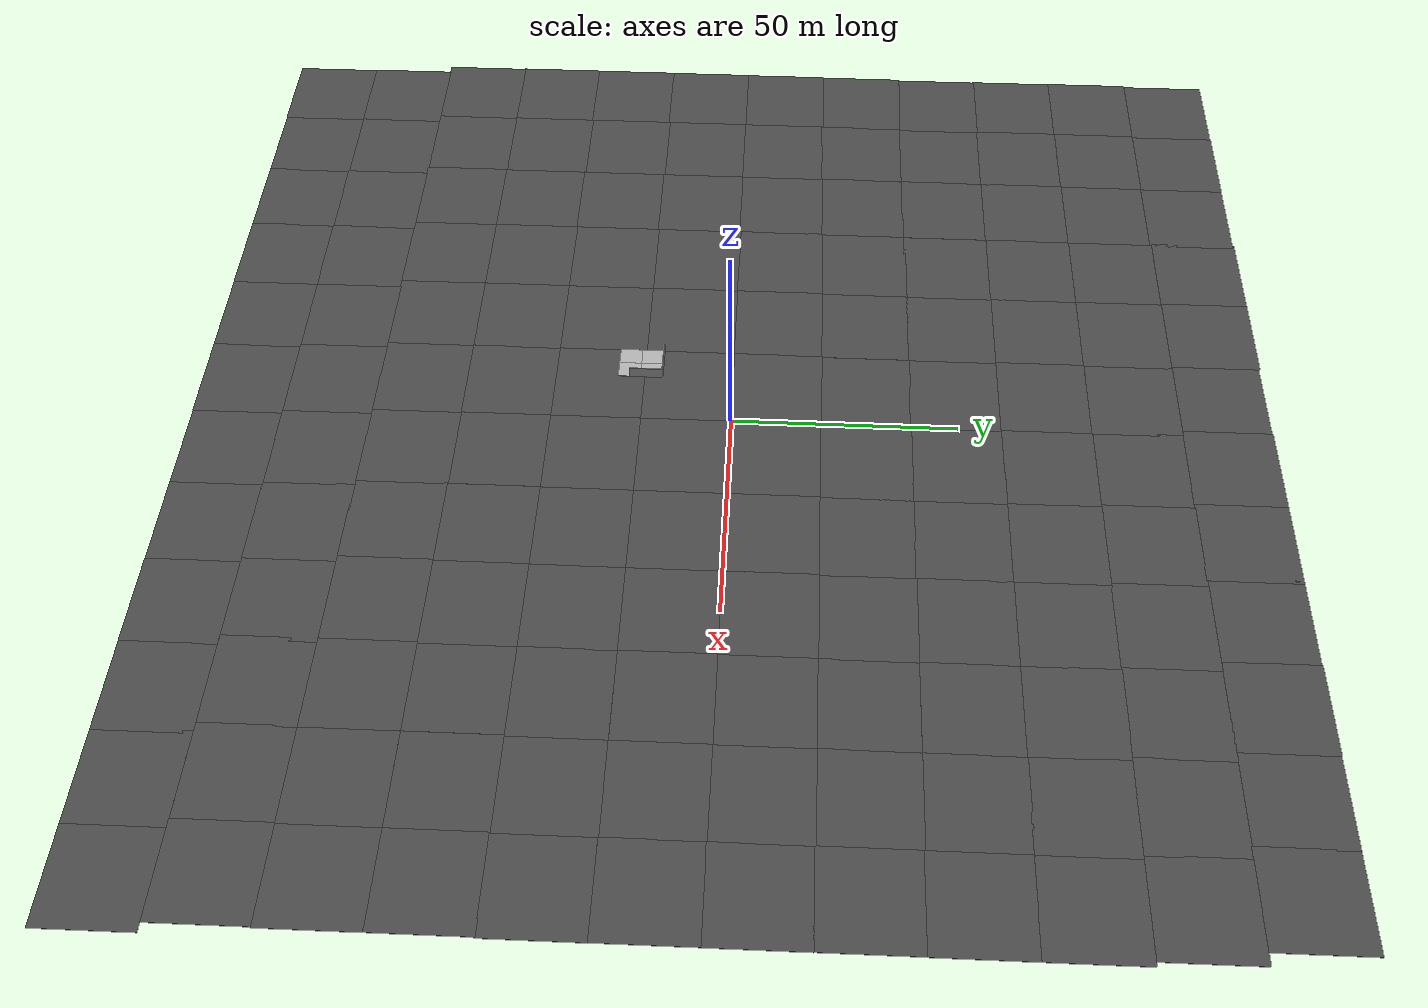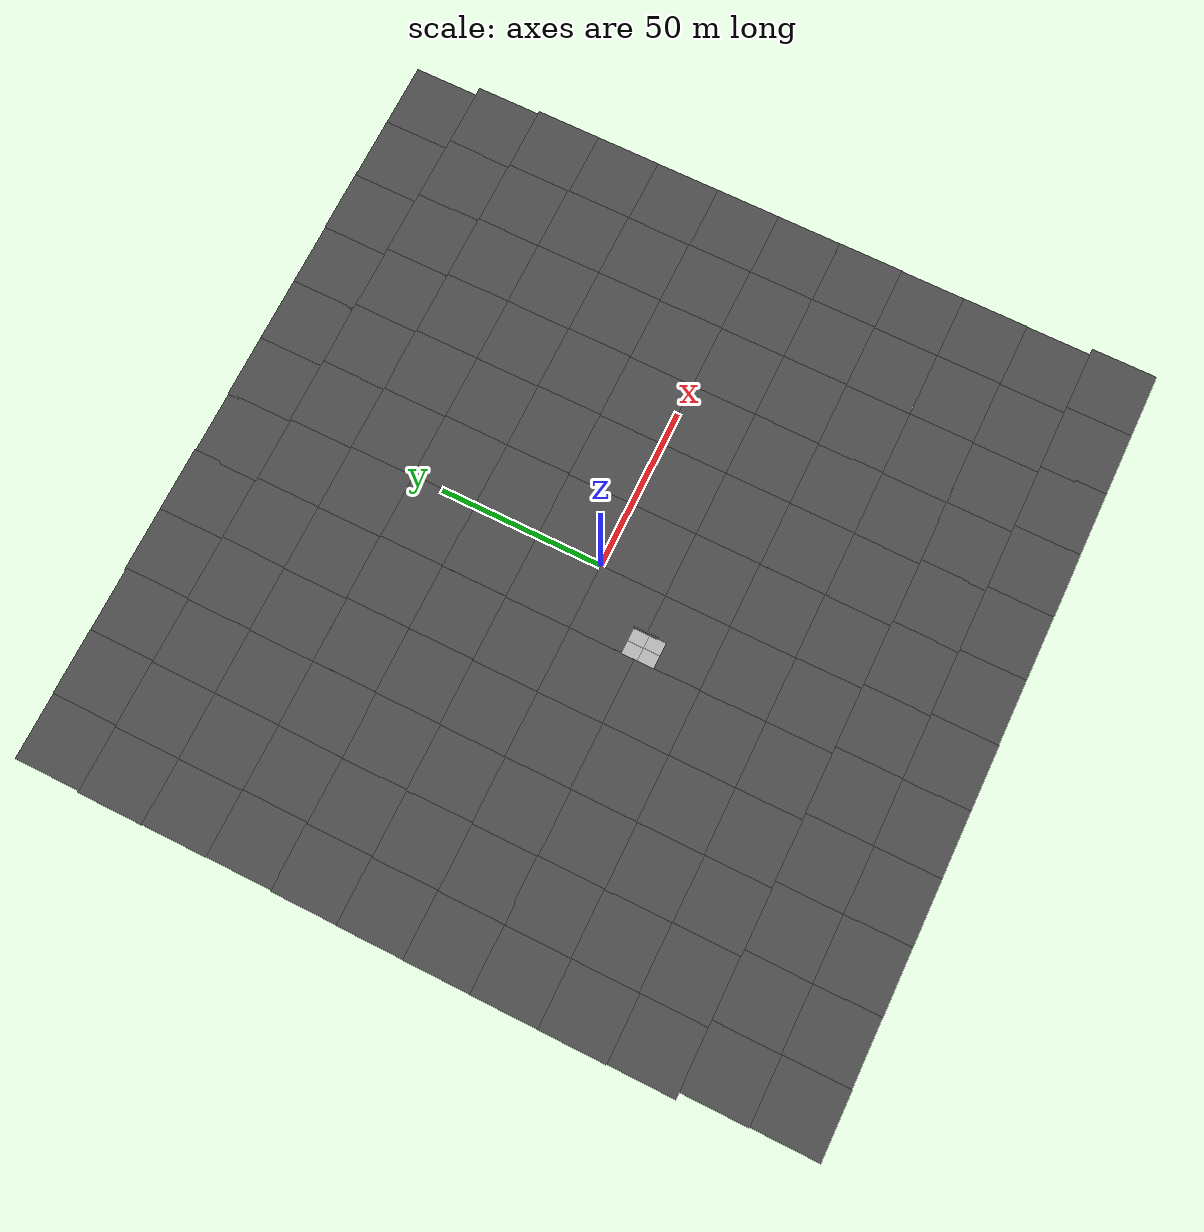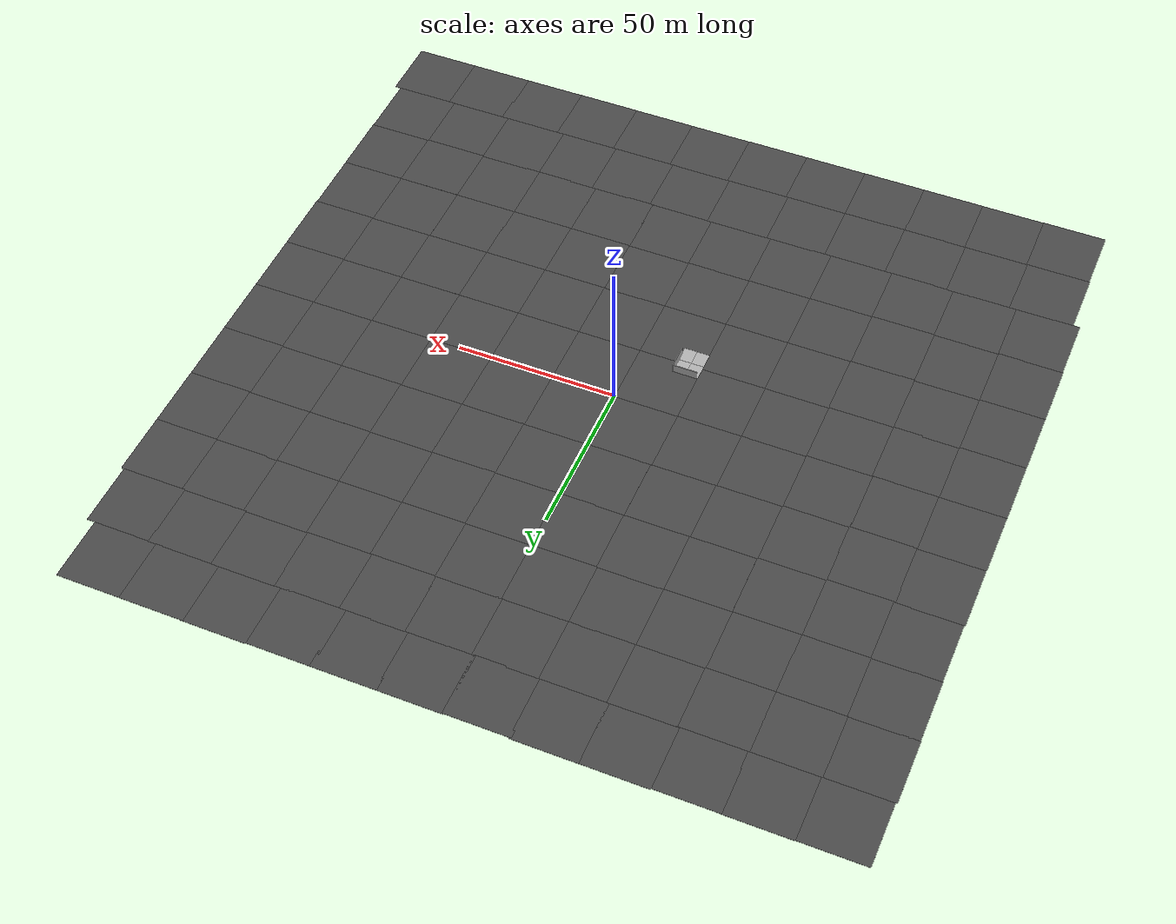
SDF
<sdf version="1.6">
 <world name="default">
  <plugin name="gazebo_octomap" filename="librotors_gazebo_octomap_plugin.so"/>
  <light name="sun" type="directional">
   <pose>0 0 10 0 -0 0</pose>
   <diffuse>0.8 0.8 0.8 1</diffuse>
   <specular>0.2 0.2 0.2 1</specular>
   <attenuation>
    <range>1000</range>
    <constant>0.9</constant>
    <linear>0.01</linear>
    <quadratic>0.001</quadratic>
   </attenuation>
   <direction>-0.5 0.1 -0.9</direction>
  </light>
  <physics name="default_physics" default="0" type="ode">
   <ode>
    <solver>
     <type>quick</type>
     <iters>1000</iters>
     <sor>1.3</sor>
     <use_dynamic_moi_rescaling>0</use_dynamic_moi_rescaling>
    </solver>
    <constraints>
     <cfm>0</cfm>
     <erp>0.2</erp>
     <contact_max_correcting_vel>100</contact_max_correcting_vel>
     <contact_surface_layer>0.001</contact_surface_layer>
    </constraints>
   </ode>
   <max_step_size>0.01</max_step_size>
   <real_time_factor>1</real_time_factor>
   <real_time_update_rate>100</real_time_update_rate>
  </physics>
  <scene><ambient>0.4 0.4 0.4 1</ambient><background>0.7 0.7 0.7 1</background><shadows>1</shadows></scene>
  <spherical_coordinates>
   <surface_model>EARTH_WGS84</surface_model>
   <latitude_deg>0</latitude_deg>
   <longitude_deg>0</longitude_deg>
   <elevation>0</elevation>
   <heading_deg>0</heading_deg>
  </spherical_coordinates>
  <model name="asphalt_plane">
   <static>1</static>
   <link name="link">
    <collision name="collision"><geometry><box><size>20 20 0.1</size></box></geometry></collision>
    <visual name="visual">
     <cast_shadows>0</cast_shadows>
     <geometry><box><size>20 20 0.1</size></box></geometry>
     <material>
      <script>
       <uri>model://asphalt_plane/materials/scripts</uri>
       <uri>model://asphalt_plane/materials/textures</uri>
       <name>vrc/asphalt</name>
      </script>
     </material>
    </visual>
    <velocity_decay><linear>0</linear><angular>0</angular></velocity_decay>
   </link>
   <pose>10 10 0 0 -0 0</pose>
  </model>
  <model name="asphalt_plane_0">
   <static>1</static>
   <link name="link">
    <collision name="collision"><geometry><box><size>20 20 0.1</size></box></geometry></collision>
    <visual name="visual">
     <cast_shadows>0</cast_shadows>
     <geometry><box><size>20 20 0.1</size></box></geometry>
     <material>
      <script>
       <uri>model://asphalt_plane/materials/scripts</uri>
       <uri>model://asphalt_plane/materials/textures</uri>
       <name>vrc/asphalt</name>
      </script>
     </material>
    </visual>
    <velocity_decay><linear>0</linear><angular>0</angular></velocity_decay>
   </link>
   <pose>10 -10 0 0 -0 0</pose>
  </model>
  <model name="asphalt_plane_1">
   <static>1</static>
   <link name="link">
    <collision name="collision"><geometry><box><size>20 20 0.1</size></box></geometry></collision>
    <visual name="visual">
     <cast_shadows>0</cast_shadows>
     <geometry><box><size>20 20 0.1</size></box></geometry>
     <material>
      <script>
       <uri>model://asphalt_plane/materials/scripts</uri>
       <uri>model://asphalt_plane/materials/textures</uri>
       <name>vrc/asphalt</name>
      </script>
     </material>
    </visual>
    <velocity_decay><linear>0</linear><angular>0</angular></velocity_decay>
   </link>
   <pose>-10 10 0 0 -0 0</pose>
  </model>
  <model name="asphalt_plane_2">
   <static>1</static>
   <link name="link">
    <collision name="collision"><geometry><box><size>20 20 0.1</size></box></geometry></collision>
    <visual name="visual">
     <cast_shadows>0</cast_shadows>
     <geometry><box><size>20 20 0.1</size></box></geometry>
     <material>
      <script>
       <uri>model://asphalt_plane/materials/scripts</uri>
       <uri>model://asphalt_plane/materials/textures</uri>
       <name>vrc/asphalt</name>
      </script>
     </material>
    </visual>
    <velocity_decay><linear>0</linear><angular>0</angular></velocity_decay>
   </link>
   <pose>-10 -10 0 0 -0 0</pose>
  </model>
  <model name="asphalt_plane_3">
   <static>1</static>
   <link name="link">
    <collision name="collision"><geometry><box><size>20 20 0.1</size></box></geometry></collision>
    <visual name="visual">
     <cast_shadows>0</cast_shadows>
     <geometry><box><size>20 20 0.1</size></box></geometry>
     <material>
      <script>
       <uri>model://asphalt_plane/materials/scripts</uri>
       <uri>model://asphalt_plane/materials/textures</uri>
       <name>vrc/asphalt</name>
      </script>
     </material>
    </visual>
    <velocity_decay><linear>0</linear><angular>0</angular></velocity_decay>
   </link>
   <pose>-10 -30 0 0 -0 0</pose>
  </model>
  <model name="asphalt_plane_4">
   <static>1</static>
   <link name="link">
    <collision name="collision"><geometry><box><size>20 20 0.1</size></box></geometry></collision>
    <visual name="visual">
     <cast_shadows>0</cast_shadows>
     <geometry><box><size>20 20 0.1</size></box></geometry>
     <material>
      <script>
       <uri>model://asphalt_plane/materials/scripts</uri>
       <uri>model://asphalt_plane/materials/textures</uri>
       <name>vrc/asphalt</name>
      </script>
     </material>
    </visual>
    <velocity_decay><linear>0</linear><angular>0</angular></velocity_decay>
   </link>
   <pose>10 -30 0 0 -0 0</pose>
  </model>
  <model name="asphalt_plane_5">
   <static>1</static>
   <link name="link">
    <collision name="collision"><geometry><box><size>20 20 0.1</size></box></geometry></collision>
    <visual name="visual">
     <cast_shadows>0</cast_shadows>
     <geometry><box><size>20 20 0.1</size></box></geometry>
     <material>
      <script>
       <uri>model://asphalt_plane/materials/scripts</uri>
       <uri>model://asphalt_plane/materials/textures</uri>
       <name>vrc/asphalt</name>
      </script>
     </material>
    </visual>
    <velocity_decay><linear>0</linear><angular>0</angular></velocity_decay>
   </link>
   <pose>30 -30 0 0 -0 0</pose>
  </model>
  <model name="asphalt_plane_6">
   <static>1</static>
   <link name="link">
    <collision name="collision"><geometry><box><size>20 20 0.1</size></box></geometry></collision>
    <visual name="visual">
     <cast_shadows>0</cast_shadows>
     <geometry><box><size>20 20 0.1</size></box></geometry>
     <material>
      <script>
       <uri>model://asphalt_plane/materials/scripts</uri>
       <uri>model://asphalt_plane/materials/textures</uri>
       <name>vrc/asphalt</name>
      </script>
     </material>
    </visual>
    <velocity_decay><linear>0</linear><angular>0</angular></velocity_decay>
   </link>
   <pose>30 10 0 0 -0 0</pose>
  </model>
  <model name="asphalt_plane_7">
   <static>1</static>
   <link name="link">
    <collision name="collision"><geometry><box><size>20 20 0.1</size></box></geometry></collision>
    <visual name="visual">
     <cast_shadows>0</cast_shadows>
     <geometry><box><size>20 20 0.1</size></box></geometry>
     <material>
      <script>
       <uri>model://asphalt_plane/materials/scripts</uri>
       <uri>model://asphalt_plane/materials/textures</uri>
       <name>vrc/asphalt</name>
      </script>
     </material>
    </visual>
    <velocity_decay><linear>0</linear><angular>0</angular></velocity_decay>
   </link>
   <pose>30 -10 0 0 -0 0</pose>
  </model>
  <model name="mud_box">
   <static>1</static>
   <link name="link">
    <collision name="collision"><geometry><box><size>8 10 0.2</size></box></geometry></collision>
    <visual name="visual_1">
     <pose>-2 2.5 0 0 -0 0</pose>
     <cast_shadows>0</cast_shadows>
     <geometry><box><size>4 5 0.2</size></box></geometry>
     <material>
      <script>
       <uri>model://mud_box/materials/scripts</uri>
       <uri>model://mud_box/materials/textures</uri>
       <name>vrc/mud</name>
      </script>
     </material>
    </visual>
    <visual name="visual_2">
     <pose>2 2.5 0 0 -0 0</pose>
     <cast_shadows>0</cast_shadows>
     <geometry><box><size>4 5 0.2</size></box></geometry>
     <material>
      <script>
       <uri>model://mud_box/materials/scripts</uri>
       <uri>model://mud_box/materials/textures</uri>
       <name>vrc/mud</name>
      </script>
     </material>
    </visual>
    <visual name="visual_3">
     <pose>2 -2.5 0 0 -0 0</pose>
     <cast_shadows>0</cast_shadows>
     <geometry><box><size>4 5 0.2</size></box></geometry>
     <material>
      <script>
       <uri>model://mud_box/materials/scripts</uri>
       <uri>model://mud_box/materials/textures</uri>
       <name>vrc/mud</name>
      </script>
     </material>
    </visual>
    <visual name="visual_4">
     <pose>-2 -2.5 0 0 -0 0</pose>
     <cast_shadows>0</cast_shadows>
     <geometry><box><size>4 5 0.2</size></box></geometry>
     <material>
      <script>
       <uri>model://mud_box/materials/scripts</uri>
       <uri>model://mud_box/materials/textures</uri>
       <name>vrc/mud</name>
      </script>
     </material>
    </visual>
    <velocity_decay><linear>0</linear><angular>0</angular></velocity_decay>
   </link>
   <pose>-16.1 -21 0 0 -0 0</pose>
  </model>
  <model name="grey_wall">
   <static>1</static>
   <link name="link">
    <pose>0 0 1.4 0 -0 0</pose>
    <collision name="collision"><geometry><box><size>7.5 0.2 2.8</size></box></geometry></collision>
    <visual name="visual">
     <cast_shadows>0</cast_shadows>
     <geometry><box><size>7.5 0.2 2.8</size></box></geometry>
     <material>
      <script>
       <uri>model://grey_wall/materials/scripts</uri>
       <uri>model://grey_wall/materials/textures</uri>
       <name>vrc/grey_wall</name>
      </script>
     </material>
    </visual>
    <velocity_decay><linear>0</linear><angular>0</angular></velocity_decay>
   </link>
   <pose>-16 -16 0 0 -0 0</pose>
  </model>
  <model name="grey_wall_0">
   <static>1</static>
   <link name="link">
    <pose>0 0 1.4 0 -0 0</pose>
    <collision name="collision"><geometry><box><size>7.5 0.2 2.8</size></box></geometry></collision>
    <visual name="visual">
     <cast_shadows>0</cast_shadows>
     <geometry><box><size>7.5 0.2 2.8</size></box></geometry>
     <material>
      <script>
       <uri>model://grey_wall/materials/scripts</uri>
       <uri>model://grey_wall/materials/textures</uri>
       <name>vrc/grey_wall</name>
      </script>
     </material>
    </visual>
    <velocity_decay><linear>0</linear><angular>0</angular></velocity_decay>
   </link>
   <pose>-12.15 -19.7 0 0 0 -1.57378</pose>
  </model>
  <gravity>0 0 -9.8</gravity>
  <magnetic_field>6e-06 2.3e-05 -4.2e-05</magnetic_field>
  <atmosphere type="adiabatic"/>
  <model name="asphalt_plane_8">
   <static>1</static>
   <link name="link">
    <collision name="collision"><geometry><box><size>20 20 0.1</size></box></geometry></collision>
    <visual name="visual">
     <cast_shadows>0</cast_shadows>
     <geometry><box><size>20 20 0.1</size></box></geometry>
     <material>
      <script>
       <uri>model://asphalt_plane/materials/scripts</uri>
       <uri>model://asphalt_plane/materials/textures</uri>
       <name>vrc/asphalt</name>
      </script>
     </material>
    </visual>
   </link>
   <pose>-10.0262 -49.9694 0 0 -0 0</pose>
  </model>
  <model name="asphalt_plane_9">
   <static>1</static>
   <link name="link">
    <collision name="collision"><geometry><box><size>20 20 0.1</size></box></geometry></collision>
    <visual name="visual">
     <cast_shadows>0</cast_shadows>
     <geometry><box><size>20 20 0.1</size></box></geometry>
     <material>
      <script>
       <uri>model://asphalt_plane/materials/scripts</uri>
       <uri>model://asphalt_plane/materials/textures</uri>
       <name>vrc/asphalt</name>
      </script>
     </material>
    </visual>
   </link>
   <pose>9.90497 -49.8349 0 0 -0 0</pose>
  </model>
  <model name="asphalt_plane_10">
   <static>1</static>
   <link name="link">
    <collision name="collision"><geometry><box><size>20 20 0.1</size></box></geometry></collision>
    <visual name="visual">
     <cast_shadows>0</cast_shadows>
     <geometry><box><size>20 20 0.1</size></box></geometry>
     <material>
      <script>
       <uri>model://asphalt_plane/materials/scripts</uri>
       <uri>model://asphalt_plane/materials/textures</uri>
       <name>vrc/asphalt</name>
      </script>
     </material>
    </visual>
   </link>
   <pose>29.9112 -49.9814 0 0 -0 0</pose>
  </model>
  <model name="asphalt_plane_11">
   <static>1</static>
   <link name="link">
    <collision name="collision"><geometry><box><size>20 20 0.1</size></box></geometry></collision>
    <visual name="visual">
     <cast_shadows>0</cast_shadows>
     <geometry><box><size>20 20 0.1</size></box></geometry>
     <material>
      <script>
       <uri>model://asphalt_plane/materials/scripts</uri>
       <uri>model://asphalt_plane/materials/textures</uri>
       <name>vrc/asphalt</name>
      </script>
     </material>
    </visual>
   </link>
   <pose>49.8726 -49.9956 0 0 -0 0</pose>
  </model>
  <model name="asphalt_plane_12">
   <static>1</static>
   <link name="link">
    <collision name="collision"><geometry><box><size>20 20 0.1</size></box></geometry></collision>
    <visual name="visual">
     <cast_shadows>0</cast_shadows>
     <geometry><box><size>20 20 0.1</size></box></geometry>
     <material>
      <script>
       <uri>model://asphalt_plane/materials/scripts</uri>
       <uri>model://asphalt_plane/materials/textures</uri>
       <name>vrc/asphalt</name>
      </script>
     </material>
    </visual>
   </link>
   <pose>49.9437 -30.008 0 0 -0 0</pose>
  </model>
  <model name="asphalt_plane_13">
   <static>1</static>
   <link name="link">
    <collision name="collision"><geometry><box><size>20 20 0.1</size></box></geometry></collision>
    <visual name="visual">
     <cast_shadows>0</cast_shadows>
     <geometry><box><size>20 20 0.1</size></box></geometry>
     <material>
      <script>
       <uri>model://asphalt_plane/materials/scripts</uri>
       <uri>model://asphalt_plane/materials/textures</uri>
       <name>vrc/asphalt</name>
      </script>
     </material>
    </visual>
   </link>
   <pose>49.8627 -10.0106 0 0 -0 0</pose>
  </model>
  <model name="asphalt_plane_14">
   <static>1</static>
   <link name="link">
    <collision name="collision"><geometry><box><size>20 20 0.1</size></box></geometry></collision>
    <visual name="visual">
     <cast_shadows>0</cast_shadows>
     <geometry><box><size>20 20 0.1</size></box></geometry>
     <material>
      <script>
       <uri>model://asphalt_plane/materials/scripts</uri>
       <uri>model://asphalt_plane/materials/textures</uri>
       <name>vrc/asphalt</name>
      </script>
     </material>
    </visual>
   </link>
   <pose>49.9112 9.97274 0 0 -0 0</pose>
  </model>
  <model name="asphalt_plane_15">
   <static>1</static>
   <link name="link">
    <collision name="collision"><geometry><box><size>20 20 0.1</size></box></geometry></collision>
    <visual name="visual">
     <cast_shadows>0</cast_shadows>
     <geometry><box><size>20 20 0.1</size></box></geometry>
     <material>
      <script>
       <uri>model://asphalt_plane/materials/scripts</uri>
       <uri>model://asphalt_plane/materials/textures</uri>
       <name>vrc/asphalt</name>
      </script>
     </material>
    </visual>
   </link>
   <pose>69.8724 9.89817 0 0 -0 0</pose>
  </model>
  <model name="asphalt_plane_16">
   <static>1</static>
   <link name="link">
    <collision name="collision"><geometry><box><size>20 20 0.1</size></box></geometry></collision>
    <visual name="visual">
     <cast_shadows>0</cast_shadows>
     <geometry><box><size>20 20 0.1</size></box></geometry>
     <material>
      <script>
       <uri>model://asphalt_plane/materials/scripts</uri>
       <uri>model://asphalt_plane/materials/textures</uri>
       <name>vrc/asphalt</name>
      </script>
     </material>
    </visual>
   </link>
   <pose>69.7476 -9.99153 0 0 -0 0</pose>
  </model>
  <model name="asphalt_plane_17">
   <static>1</static>
   <link name="link">
    <collision name="collision"><geometry><box><size>20 20 0.1</size></box></geometry></collision>
    <visual name="visual">
     <cast_shadows>0</cast_shadows>
     <geometry><box><size>20 20 0.1</size></box></geometry>
     <material>
      <script>
       <uri>model://asphalt_plane/materials/scripts</uri>
       <uri>model://asphalt_plane/materials/textures</uri>
       <name>vrc/asphalt</name>
      </script>
     </material>
    </visual>
   </link>
   <pose>69.7642 -29.9969 0 0 -0 0</pose>
  </model>
  <model name="asphalt_plane_18">
   <static>1</static>
   <link name="link">
    <collision name="collision"><geometry><box><size>20 20 0.1</size></box></geometry></collision>
    <visual name="visual">
     <cast_shadows>0</cast_shadows>
     <geometry><box><size>20 20 0.1</size></box></geometry>
     <material>
      <script>
       <uri>model://asphalt_plane/materials/scripts</uri>
       <uri>model://asphalt_plane/materials/textures</uri>
       <name>vrc/asphalt</name>
      </script>
     </material>
    </visual>
   </link>
   <pose>89.7409 -29.9732 0 0 -0 0</pose>
  </model>
  <model name="asphalt_plane_19">
   <static>1</static>
   <link name="link">
    <collision name="collision"><geometry><box><size>20 20 0.1</size></box></geometry></collision>
    <visual name="visual">
     <cast_shadows>0</cast_shadows>
     <geometry><box><size>20 20 0.1</size></box></geometry>
     <material>
      <script>
       <uri>model://asphalt_plane/materials/scripts</uri>
       <uri>model://asphalt_plane/materials/textures</uri>
       <name>vrc/asphalt</name>
      </script>
     </material>
    </visual>
   </link>
   <pose>69.5165 -49.9575 0 0 -0 0</pose>
  </model>
  <model name="asphalt_plane_20">
   <static>1</static>
   <link name="link">
    <collision name="collision"><geometry><box><size>20 20 0.1</size></box></geometry></collision>
    <visual name="visual">
     <cast_shadows>0</cast_shadows>
     <geometry><box><size>20 20 0.1</size></box></geometry>
     <material>
      <script>
       <uri>model://asphalt_plane/materials/scripts</uri>
       <uri>model://asphalt_plane/materials/textures</uri>
       <name>vrc/asphalt</name>
      </script>
     </material>
    </visual>
   </link>
   <pose>89.524 -49.9377 0 0 -0 0</pose>
  </model>
  <model name="asphalt_plane_21">
   <static>1</static>
   <link name="link">
    <collision name="collision"><geometry><box><size>20 20 0.1</size></box></geometry></collision>
    <visual name="visual">
     <cast_shadows>0</cast_shadows>
     <geometry><box><size>20 20 0.1</size></box></geometry>
     <material>
      <script>
       <uri>model://asphalt_plane/materials/scripts</uri>
       <uri>model://asphalt_plane/materials/textures</uri>
       <name>vrc/asphalt</name>
      </script>
     </material>
    </visual>
   </link>
   <pose>89.7231 -10.0366 0 0 -0 0</pose>
  </model>
  <model name="asphalt_plane_22">
   <static>1</static>
   <link name="link">
    <collision name="collision"><geometry><box><size>20 20 0.1</size></box></geometry></collision>
    <visual name="visual">
     <cast_shadows>0</cast_shadows>
     <geometry><box><size>20 20 0.1</size></box></geometry>
     <material>
      <script>
       <uri>model://asphalt_plane/materials/scripts</uri>
       <uri>model://asphalt_plane/materials/textures</uri>
       <name>vrc/asphalt</name>
      </script>
     </material>
    </visual>
   </link>
   <pose>89.7247 9.89413 0 0 -0 0</pose>
  </model>
  <model name="asphalt_plane_23">
   <static>1</static>
   <link name="link">
    <collision name="collision"><geometry><box><size>20 20 0.1</size></box></geometry></collision>
    <visual name="visual">
     <cast_shadows>0</cast_shadows>
     <geometry><box><size>20 20 0.1</size></box></geometry>
     <material>
      <script>
       <uri>model://asphalt_plane/materials/scripts</uri>
       <uri>model://asphalt_plane/materials/textures</uri>
       <name>vrc/asphalt</name>
      </script>
     </material>
    </visual>
   </link>
   <pose>89.7547 29.8835 0 0 -0 0</pose>
  </model>
  <model name="asphalt_plane_24">
   <static>1</static>
   <link name="link">
    <collision name="collision"><geometry><box><size>20 20 0.1</size></box></geometry></collision>
    <visual name="visual">
     <cast_shadows>0</cast_shadows>
     <geometry><box><size>20 20 0.1</size></box></geometry>
     <material>
      <script>
       <uri>model://asphalt_plane/materials/scripts</uri>
       <uri>model://asphalt_plane/materials/textures</uri>
       <name>vrc/asphalt</name>
      </script>
     </material>
    </visual>
   </link>
   <pose>69.8832 29.8469 0 0 -0 0</pose>
  </model>
  <model name="asphalt_plane_25">
   <static>1</static>
   <link name="link">
    <collision name="collision"><geometry><box><size>20 20 0.1</size></box></geometry></collision>
    <visual name="visual">
     <cast_shadows>0</cast_shadows>
     <geometry><box><size>20 20 0.1</size></box></geometry>
     <material>
      <script>
       <uri>model://asphalt_plane/materials/scripts</uri>
       <uri>model://asphalt_plane/materials/textures</uri>
       <name>vrc/asphalt</name>
      </script>
     </material>
    </visual>
   </link>
   <pose>50.1313 29.9342 0 0 -0 0</pose>
  </model>
  <model name="asphalt_plane_26">
   <static>1</static>
   <link name="link">
    <collision name="collision"><geometry><box><size>20 20 0.1</size></box></geometry></collision>
    <visual name="visual">
     <cast_shadows>0</cast_shadows>
     <geometry><box><size>20 20 0.1</size></box></geometry>
     <material>
      <script>
       <uri>model://asphalt_plane/materials/scripts</uri>
       <uri>model://asphalt_plane/materials/textures</uri>
       <name>vrc/asphalt</name>
      </script>
     </material>
    </visual>
   </link>
   <pose>30.2259 29.8587 0 0 -0 0</pose>
  </model>
  <model name="asphalt_plane_27">
   <static>1</static>
   <link name="link">
    <collision name="collision"><geometry><box><size>20 20 0.1</size></box></geometry></collision>
    <visual name="visual">
     <cast_shadows>0</cast_shadows>
     <geometry><box><size>20 20 0.1</size></box></geometry>
     <material>
      <script>
       <uri>model://asphalt_plane/materials/scripts</uri>
       <uri>model://asphalt_plane/materials/textures</uri>
       <name>vrc/asphalt</name>
      </script>
     </material>
    </visual>
   </link>
   <pose>10.3485 29.8638 0 0 -0 0</pose>
  </model>
  <model name="asphalt_plane_28">
   <static>1</static>
   <link name="link">
    <collision name="collision"><geometry><box><size>20 20 0.1</size></box></geometry></collision>
    <visual name="visual">
     <cast_shadows>0</cast_shadows>
     <geometry><box><size>20 20 0.1</size></box></geometry>
     <material>
      <script>
       <uri>model://asphalt_plane/materials/scripts</uri>
       <uri>model://asphalt_plane/materials/textures</uri>
       <name>vrc/asphalt</name>
      </script>
     </material>
    </visual>
   </link>
   <pose>-9.65035 29.8845 0 0 -0 0</pose>
  </model>
  <model name="asphalt_plane_29">
   <static>1</static>
   <link name="link">
    <collision name="collision"><geometry><box><size>20 20 0.1</size></box></geometry></collision>
    <visual name="visual">
     <cast_shadows>0</cast_shadows>
     <geometry><box><size>20 20 0.1</size></box></geometry>
     <material>
      <script>
       <uri>model://asphalt_plane/materials/scripts</uri>
       <uri>model://asphalt_plane/materials/textures</uri>
       <name>vrc/asphalt</name>
      </script>
     </material>
    </visual>
   </link>
   <pose>-29.6635 29.8636 0 0 -0 0</pose>
  </model>
  <model name="asphalt_plane_30">
   <static>1</static>
   <link name="link">
    <collision name="collision"><geometry><box><size>20 20 0.1</size></box></geometry></collision>
    <visual name="visual">
     <cast_shadows>0</cast_shadows>
     <geometry><box><size>20 20 0.1</size></box></geometry>
     <material>
      <script>
       <uri>model://asphalt_plane/materials/scripts</uri>
       <uri>model://asphalt_plane/materials/textures</uri>
       <name>vrc/asphalt</name>
      </script>
     </material>
    </visual>
   </link>
   <pose>-29.8719 9.89328 0 0 -0 0</pose>
  </model>
  <model name="asphalt_plane_31">
   <static>1</static>
   <link name="link">
    <collision name="collision"><geometry><box><size>20 20 0.1</size></box></geometry></collision>
    <visual name="visual">
     <cast_shadows>0</cast_shadows>
     <geometry><box><size>20 20 0.1</size></box></geometry>
     <material>
      <script>
       <uri>model://asphalt_plane/materials/scripts</uri>
       <uri>model://asphalt_plane/materials/textures</uri>
       <name>vrc/asphalt</name>
      </script>
     </material>
    </visual>
   </link>
   <pose>-29.9029 -10.0926 0 0 -0 0</pose>
  </model>
  <model name="asphalt_plane_32">
   <static>1</static>
   <link name="link">
    <collision name="collision"><geometry><box><size>20 20 0.1</size></box></geometry></collision>
    <visual name="visual">
     <cast_shadows>0</cast_shadows>
     <geometry><box><size>20 20 0.1</size></box></geometry>
     <material>
      <script>
       <uri>model://asphalt_plane/materials/scripts</uri>
       <uri>model://asphalt_plane/materials/textures</uri>
       <name>vrc/asphalt</name>
      </script>
     </material>
    </visual>
   </link>
   <pose>-29.8516 -30.0257 0 0 -0 0</pose>
  </model>
  <model name="asphalt_plane_33">
   <static>1</static>
   <link name="link">
    <collision name="collision"><geometry><box><size>20 20 0.1</size></box></geometry></collision>
    <visual name="visual">
     <cast_shadows>0</cast_shadows>
     <geometry><box><size>20 20 0.1</size></box></geometry>
     <material>
      <script>
       <uri>model://asphalt_plane/materials/scripts</uri>
       <uri>model://asphalt_plane/materials/textures</uri>
       <name>vrc/asphalt</name>
      </script>
     </material>
    </visual>
   </link>
   <pose>-29.8339 -50.017 0 0 -0 0</pose>
  </model>
  <model name="asphalt_plane_34">
   <static>1</static>
   <link name="link">
    <collision name="collision"><geometry><box><size>20 20 0.1</size></box></geometry></collision>
    <visual name="visual">
     <cast_shadows>0</cast_shadows>
     <geometry><box><size>20 20 0.1</size></box></geometry>
     <material>
      <script>
       <uri>model://asphalt_plane/materials/scripts</uri>
       <uri>model://asphalt_plane/materials/textures</uri>
       <name>vrc/asphalt</name>
      </script>
     </material>
    </visual>
   </link>
   <pose>-49.8045 -50.0177 0 0 -0 0</pose>
  </model>
  <model name="asphalt_plane_35">
   <static>1</static>
   <link name="link">
    <collision name="collision"><geometry><box><size>20 20 0.1</size></box></geometry></collision>
    <visual name="visual">
     <cast_shadows>0</cast_shadows>
     <geometry><box><size>20 20 0.1</size></box></geometry>
     <material>
      <script>
       <uri>model://asphalt_plane/materials/scripts</uri>
       <uri>model://asphalt_plane/materials/textures</uri>
       <name>vrc/asphalt</name>
      </script>
     </material>
    </visual>
   </link>
   <pose>-49.7739 -30.0396 0 0 -0 0</pose>
  </model>
  <model name="asphalt_plane_36">
   <static>1</static>
   <link name="link">
    <collision name="collision"><geometry><box><size>20 20 0.1</size></box></geometry></collision>
    <visual name="visual">
     <cast_shadows>0</cast_shadows>
     <geometry><box><size>20 20 0.1</size></box></geometry>
     <material>
      <script>
       <uri>model://asphalt_plane/materials/scripts</uri>
       <uri>model://asphalt_plane/materials/textures</uri>
       <name>vrc/asphalt</name>
      </script>
     </material>
    </visual>
   </link>
   <pose>-49.7315 -10.0641 0 0 -0 0</pose>
  </model>
  <model name="asphalt_plane_37">
   <static>1</static>
   <link name="link">
    <collision name="collision"><geometry><box><size>20 20 0.1</size></box></geometry></collision>
    <visual name="visual">
     <cast_shadows>0</cast_shadows>
     <geometry><box><size>20 20 0.1</size></box></geometry>
     <material>
      <script>
       <uri>model://asphalt_plane/materials/scripts</uri>
       <uri>model://asphalt_plane/materials/textures</uri>
       <name>vrc/asphalt</name>
      </script>
     </material>
    </visual>
   </link>
   <pose>-49.8526 9.81961 0 0 -0 0</pose>
  </model>
  <model name="asphalt_plane_38">
   <static>1</static>
   <link name="link">
    <collision name="collision"><geometry><box><size>20 20 0.1</size></box></geometry></collision>
    <visual name="visual">
     <cast_shadows>0</cast_shadows>
     <geometry><box><size>20 20 0.1</size></box></geometry>
     <material>
      <script>
       <uri>model://asphalt_plane/materials/scripts</uri>
       <uri>model://asphalt_plane/materials/textures</uri>
       <name>vrc/asphalt</name>
      </script>
     </material>
    </visual>
   </link>
   <pose>-49.5858 29.8157 0 0 -0 0</pose>
  </model>
  <model name="asphalt_plane_39">
   <static>1</static>
   <link name="link">
    <collision name="collision"><geometry><box><size>20 20 0.1</size></box></geometry></collision>
    <visual name="visual">
     <cast_shadows>0</cast_shadows>
     <geometry><box><size>20 20 0.1</size></box></geometry>
     <material>
      <script>
       <uri>model://asphalt_plane/materials/scripts</uri>
       <uri>model://asphalt_plane/materials/textures</uri>
       <name>vrc/asphalt</name>
      </script>
     </material>
    </visual>
   </link>
   <pose>-69.7888 -50.1931 0 0 -0 0</pose>
  </model>
  <model name="asphalt_plane_40">
   <static>1</static>
   <link name="link">
    <collision name="collision"><geometry><box><size>20 20 0.1</size></box></geometry></collision>
    <visual name="visual">
     <cast_shadows>0</cast_shadows>
     <geometry><box><size>20 20 0.1</size></box></geometry>
     <material>
      <script>
       <uri>model://asphalt_plane/materials/scripts</uri>
       <uri>model://asphalt_plane/materials/textures</uri>
       <name>vrc/asphalt</name>
      </script>
     </material>
    </visual>
   </link>
   <pose>-69.5889 -30.305 0 0 -0 0</pose>
  </model>
  <model name="asphalt_plane_41">
   <static>1</static>
   <link name="link">
    <collision name="collision"><geometry><box><size>20 20 0.1</size></box></geometry></collision>
    <visual name="visual">
     <cast_shadows>0</cast_shadows>
     <geometry><box><size>20 20 0.1</size></box></geometry>
     <material>
      <script>
       <uri>model://asphalt_plane/materials/scripts</uri>
       <uri>model://asphalt_plane/materials/textures</uri>
       <name>vrc/asphalt</name>
      </script>
     </material>
    </visual>
   </link>
   <pose>-69.6926 -10.3768 0 0 -0 0</pose>
  </model>
  <model name="asphalt_plane_42">
   <static>1</static>
   <link name="link">
    <collision name="collision"><geometry><box><size>20 20 0.1</size></box></geometry></collision>
    <visual name="visual">
     <cast_shadows>0</cast_shadows>
     <geometry><box><size>20 20 0.1</size></box></geometry>
     <material>
      <script>
       <uri>model://asphalt_plane/materials/scripts</uri>
       <uri>model://asphalt_plane/materials/textures</uri>
       <name>vrc/asphalt</name>
      </script>
     </material>
    </visual>
   </link>
   <pose>-69.7195 9.5907 0 0 -0 0</pose>
  </model>
  <model name="asphalt_plane_43">
   <static>1</static>
   <link name="link">
    <collision name="collision"><geometry><box><size>20 20 0.1</size></box></geometry></collision>
    <visual name="visual">
     <cast_shadows>0</cast_shadows>
     <geometry><box><size>20 20 0.1</size></box></geometry>
     <material>
      <script>
       <uri>model://asphalt_plane/materials/scripts</uri>
       <uri>model://asphalt_plane/materials/textures</uri>
       <name>vrc/asphalt</name>
      </script>
     </material>
    </visual>
   </link>
   <pose>-69.5806 29.5148 0 0 -0 0</pose>
  </model>
  <model name="asphalt_plane_44">
   <static>1</static>
   <link name="link">
    <collision name="collision"><geometry><box><size>20 20 0.1</size></box></geometry></collision>
    <visual name="visual">
     <cast_shadows>0</cast_shadows>
     <geometry><box><size>20 20 0.1</size></box></geometry>
     <material>
      <script>
       <uri>model://asphalt_plane/materials/scripts</uri>
       <uri>model://asphalt_plane/materials/textures</uri>
       <name>vrc/asphalt</name>
      </script>
     </material>
    </visual>
   </link>
   <pose>-69.4546 49.2496 0 0 -0 0</pose>
  </model>
  <model name="asphalt_plane_45">
   <static>1</static>
   <link name="link">
    <collision name="collision"><geometry><box><size>20 20 0.1</size></box></geometry></collision>
    <visual name="visual">
     <cast_shadows>0</cast_shadows>
     <geometry><box><size>20 20 0.1</size></box></geometry>
     <material>
      <script>
       <uri>model://asphalt_plane/materials/scripts</uri>
       <uri>model://asphalt_plane/materials/textures</uri>
       <name>vrc/asphalt</name>
      </script>
     </material>
    </visual>
   </link>
   <pose>-49.4459 49.3852 0 0 -0 0</pose>
  </model>
  <model name="asphalt_plane_46">
   <static>1</static>
   <link name="link">
    <collision name="collision"><geometry><box><size>20 20 0.1</size></box></geometry></collision>
    <visual name="visual">
     <cast_shadows>0</cast_shadows>
     <geometry><box><size>20 20 0.1</size></box></geometry>
     <material>
      <script>
       <uri>model://asphalt_plane/materials/scripts</uri>
       <uri>model://asphalt_plane/materials/textures</uri>
       <name>vrc/asphalt</name>
      </script>
     </material>
    </visual>
   </link>
   <pose>-29.5435 49.6651 0 0 -0 0</pose>
  </model>
  <model name="asphalt_plane_47">
   <static>1</static>
   <link name="link">
    <collision name="collision"><geometry><box><size>20 20 0.1</size></box></geometry></collision>
    <visual name="visual">
     <cast_shadows>0</cast_shadows>
     <geometry><box><size>20 20 0.1</size></box></geometry>
     <material>
      <script>
       <uri>model://asphalt_plane/materials/scripts</uri>
       <uri>model://asphalt_plane/materials/textures</uri>
       <name>vrc/asphalt</name>
      </script>
     </material>
    </visual>
   </link>
   <pose>-9.54993 49.5955 0 0 -0 0</pose>
  </model>
  <model name="asphalt_plane_48">
   <static>1</static>
   <link name="link">
    <collision name="collision"><geometry><box><size>20 20 0.1</size></box></geometry></collision>
    <visual name="visual">
     <cast_shadows>0</cast_shadows>
     <geometry><box><size>20 20 0.1</size></box></geometry>
     <material>
      <script>
       <uri>model://asphalt_plane/materials/scripts</uri>
       <uri>model://asphalt_plane/materials/textures</uri>
       <name>vrc/asphalt</name>
      </script>
     </material>
    </visual>
   </link>
   <pose>10.317 49.7326 0 0 -0 0</pose>
  </model>
  <model name="asphalt_plane_49">
   <static>1</static>
   <link name="link">
    <collision name="collision"><geometry><box><size>20 20 0.1</size></box></geometry></collision>
    <visual name="visual">
     <cast_shadows>0</cast_shadows>
     <geometry><box><size>20 20 0.1</size></box></geometry>
     <material>
      <script>
       <uri>model://asphalt_plane/materials/scripts</uri>
       <uri>model://asphalt_plane/materials/textures</uri>
       <name>vrc/asphalt</name>
      </script>
     </material>
    </visual>
   </link>
   <pose>30.1956 49.6959 0 0 -0 0</pose>
  </model>
  <model name="asphalt_plane_50">
   <static>1</static>
   <link name="link">
    <collision name="collision"><geometry><box><size>20 20 0.1</size></box></geometry></collision>
    <visual name="visual">
     <cast_shadows>0</cast_shadows>
     <geometry><box><size>20 20 0.1</size></box></geometry>
     <material>
      <script>
       <uri>model://asphalt_plane/materials/scripts</uri>
       <uri>model://asphalt_plane/materials/textures</uri>
       <name>vrc/asphalt</name>
      </script>
     </material>
    </visual>
   </link>
   <pose>50.0171 49.7575 0 0 -0 0</pose>
  </model>
  <model name="asphalt_plane_51">
   <static>1</static>
   <link name="link">
    <collision name="collision"><geometry><box><size>20 20 0.1</size></box></geometry></collision>
    <visual name="visual">
     <cast_shadows>0</cast_shadows>
     <geometry><box><size>20 20 0.1</size></box></geometry>
     <material>
      <script>
       <uri>model://asphalt_plane/materials/scripts</uri>
       <uri>model://asphalt_plane/materials/textures</uri>
       <name>vrc/asphalt</name>
      </script>
     </material>
    </visual>
   </link>
   <pose>89.832 49.8753 0 0 -0 0</pose>
  </model>
  <model name="asphalt_plane_52">
   <static>1</static>
   <link name="link">
    <collision name="collision"><geometry><box><size>20 20 0.1</size></box></geometry></collision>
    <visual name="visual">
     <cast_shadows>0</cast_shadows>
     <geometry><box><size>20 20 0.1</size></box></geometry>
     <material>
      <script>
       <uri>model://asphalt_plane/materials/scripts</uri>
       <uri>model://asphalt_plane/materials/textures</uri>
       <name>vrc/asphalt</name>
      </script>
     </material>
    </visual>
   </link>
   <pose>69.9278 49.8517 0 0 -0 0</pose>
  </model>
  <model name="asphalt_plane_53">
   <static>1</static>
   <link name="link">
    <collision name="collision"><geometry><box><size>20 20 0.1</size></box></geometry></collision>
    <visual name="visual">
     <cast_shadows>0</cast_shadows>
     <geometry><box><size>20 20 0.1</size></box></geometry>
     <material>
      <script>
       <uri>model://asphalt_plane/materials/scripts</uri>
       <uri>model://asphalt_plane/materials/textures</uri>
       <name>vrc/asphalt</name>
      </script>
     </material>
    </visual>
   </link>
   <pose>89.7044 69.5615 0 0 -0 0</pose>
  </model>
  <model name="asphalt_plane_54">
   <static>1</static>
   <link name="link">
    <collision name="collision"><geometry><box><size>20 20 0.1</size></box></geometry></collision>
    <visual name="visual">
     <cast_shadows>0</cast_shadows>
     <geometry><box><size>20 20 0.1</size></box></geometry>
     <material>
      <script>
       <uri>model://asphalt_plane/materials/scripts</uri>
       <uri>model://asphalt_plane/materials/textures</uri>
       <name>vrc/asphalt</name>
      </script>
     </material>
    </visual>
   </link>
   <pose>69.8661 69.7307 0 0 -0 0</pose>
  </model>
  <model name="asphalt_plane_55">
   <static>1</static>
   <link name="link">
    <collision name="collision"><geometry><box><size>20 20 0.1</size></box></geometry></collision>
    <visual name="visual">
     <cast_shadows>0</cast_shadows>
     <geometry><box><size>20 20 0.1</size></box></geometry>
     <material>
      <script>
       <uri>model://asphalt_plane/materials/scripts</uri>
       <uri>model://asphalt_plane/materials/textures</uri>
       <name>vrc/asphalt</name>
      </script>
     </material>
    </visual>
   </link>
   <pose>50.0081 69.731 0 0 -0 0</pose>
  </model>
  <model name="asphalt_plane_56">
   <static>1</static>
   <link name="link">
    <collision name="collision"><geometry><box><size>20 20 0.1</size></box></geometry></collision>
    <visual name="visual">
     <cast_shadows>0</cast_shadows>
     <geometry><box><size>20 20 0.1</size></box></geometry>
     <material>
      <script>
       <uri>model://asphalt_plane/materials/scripts</uri>
       <uri>model://asphalt_plane/materials/textures</uri>
       <name>vrc/asphalt</name>
      </script>
     </material>
    </visual>
   </link>
   <pose>30.0508 69.6751 0 0 -0 0</pose>
  </model>
  <model name="asphalt_plane_57">
   <static>1</static>
   <link name="link">
    <collision name="collision"><geometry><box><size>20 20 0.1</size></box></geometry></collision>
    <visual name="visual">
     <cast_shadows>0</cast_shadows>
     <geometry><box><size>20 20 0.1</size></box></geometry>
     <material>
      <script>
       <uri>model://asphalt_plane/materials/scripts</uri>
       <uri>model://asphalt_plane/materials/textures</uri>
       <name>vrc/asphalt</name>
      </script>
     </material>
    </visual>
   </link>
   <pose>10.1046 69.5693 0 0 -0 0</pose>
  </model>
  <model name="asphalt_plane_58">
   <static>1</static>
   <link name="link">
    <collision name="collision"><geometry><box><size>20 20 0.1</size></box></geometry></collision>
    <visual name="visual">
     <cast_shadows>0</cast_shadows>
     <geometry><box><size>20 20 0.1</size></box></geometry>
     <material>
      <script>
       <uri>model://asphalt_plane/materials/scripts</uri>
       <uri>model://asphalt_plane/materials/textures</uri>
       <name>vrc/asphalt</name>
      </script>
     </material>
    </visual>
   </link>
   <pose>-9.86457 69.4864 0 0 -0 0</pose>
  </model>
  <model name="asphalt_plane_59">
   <static>1</static>
   <link name="link">
    <collision name="collision"><geometry><box><size>20 20 0.1</size></box></geometry></collision>
    <visual name="visual">
     <cast_shadows>0</cast_shadows>
     <geometry><box><size>20 20 0.1</size></box></geometry>
     <material>
      <script>
       <uri>model://asphalt_plane/materials/scripts</uri>
       <uri>model://asphalt_plane/materials/textures</uri>
       <name>vrc/asphalt</name>
      </script>
     </material>
    </visual>
   </link>
   <pose>-29.8012 69.5131 0 0 -0 0</pose>
  </model>
  <model name="asphalt_plane_60">
   <static>1</static>
   <link name="link">
    <collision name="collision"><geometry><box><size>20 20 0.1</size></box></geometry></collision>
    <visual name="visual">
     <cast_shadows>0</cast_shadows>
     <geometry><box><size>20 20 0.1</size></box></geometry>
     <material>
      <script>
       <uri>model://asphalt_plane/materials/scripts</uri>
       <uri>model://asphalt_plane/materials/textures</uri>
       <name>vrc/asphalt</name>
      </script>
     </material>
    </visual>
   </link>
   <pose>-49.5215 69.3867 0 0 -0 0</pose>
  </model>
  <model name="asphalt_plane_61">
   <static>1</static>
   <link name="link">
    <collision name="collision"><geometry><box><size>20 20 0.1</size></box></geometry></collision>
    <visual name="visual">
     <cast_shadows>0</cast_shadows>
     <geometry><box><size>20 20 0.1</size></box></geometry>
     <material>
      <script>
       <uri>model://asphalt_plane/materials/scripts</uri>
       <uri>model://asphalt_plane/materials/textures</uri>
       <name>vrc/asphalt</name>
      </script>
     </material>
    </visual>
   </link>
   <pose>-69.39 69.2244 0 0 -0 0</pose>
  </model>
  <model name="asphalt_plane_62">
   <static>1</static>
   <link name="link">
    <collision name="collision"><geometry><box><size>20 20 0.1</size></box></geometry></collision>
    <visual name="visual">
     <cast_shadows>0</cast_shadows>
     <geometry><box><size>20 20 0.1</size></box></geometry>
     <material>
      <script>
       <uri>model://asphalt_plane/materials/scripts</uri>
       <uri>model://asphalt_plane/materials/textures</uri>
       <name>vrc/asphalt</name>
      </script>
     </material>
    </visual>
   </link>
   <pose>89.5542 -69.9429 0 0 -0 0</pose>
  </model>
  <model name="asphalt_plane_63">
   <static>1</static>
   <link name="link">
    <collision name="collision"><geometry><box><size>20 20 0.1</size></box></geometry></collision>
    <visual name="visual">
     <cast_shadows>0</cast_shadows>
     <geometry><box><size>20 20 0.1</size></box></geometry>
     <material>
      <script>
       <uri>model://asphalt_plane/materials/scripts</uri>
       <uri>model://asphalt_plane/materials/textures</uri>
       <name>vrc/asphalt</name>
      </script>
     </material>
    </visual>
   </link>
   <pose>69.5613 -69.949 0 0 -0 0</pose>
  </model>
  <model name="asphalt_plane_64">
   <static>1</static>
   <link name="link">
    <collision name="collision"><geometry><box><size>20 20 0.1</size></box></geometry></collision>
    <visual name="visual">
     <cast_shadows>0</cast_shadows>
     <geometry><box><size>20 20 0.1</size></box></geometry>
     <material>
      <script>
       <uri>model://asphalt_plane/materials/scripts</uri>
       <uri>model://asphalt_plane/materials/textures</uri>
       <name>vrc/asphalt</name>
      </script>
     </material>
    </visual>
   </link>
   <pose>49.6276 -69.956 0 0 -0 0</pose>
  </model>
  <model name="asphalt_plane_65">
   <static>1</static>
   <link name="link">
    <collision name="collision"><geometry><box><size>20 20 0.1</size></box></geometry></collision>
    <visual name="visual">
     <cast_shadows>0</cast_shadows>
     <geometry><box><size>20 20 0.1</size></box></geometry>
     <material>
      <script>
       <uri>model://asphalt_plane/materials/scripts</uri>
       <uri>model://asphalt_plane/materials/textures</uri>
       <name>vrc/asphalt</name>
      </script>
     </material>
    </visual>
   </link>
   <pose>29.7748 -69.971 0 0 -0 0</pose>
  </model>
  <model name="asphalt_plane_66">
   <static>1</static>
   <link name="link">
    <collision name="collision"><geometry><box><size>20 20 0.1</size></box></geometry></collision>
    <visual name="visual">
     <cast_shadows>0</cast_shadows>
     <geometry><box><size>20 20 0.1</size></box></geometry>
     <material>
      <script>
       <uri>model://asphalt_plane/materials/scripts</uri>
       <uri>model://asphalt_plane/materials/textures</uri>
       <name>vrc/asphalt</name>
      </script>
     </material>
    </visual>
   </link>
   <pose>10.0475 -69.792 0 0 -0 0</pose>
  </model>
  <model name="asphalt_plane_67">
   <static>1</static>
   <link name="link">
    <collision name="collision"><geometry><box><size>20 20 0.1</size></box></geometry></collision>
    <visual name="visual">
     <cast_shadows>0</cast_shadows>
     <geometry><box><size>20 20 0.1</size></box></geometry>
     <material>
      <script>
       <uri>model://asphalt_plane/materials/scripts</uri>
       <uri>model://asphalt_plane/materials/textures</uri>
       <name>vrc/asphalt</name>
      </script>
     </material>
    </visual>
   </link>
   <pose>-9.8692 -69.8203 0 0 -0 0</pose>
  </model>
  <model name="asphalt_plane_68">
   <static>1</static>
   <link name="link">
    <collision name="collision"><geometry><box><size>20 20 0.1</size></box></geometry></collision>
    <visual name="visual">
     <cast_shadows>0</cast_shadows>
     <geometry><box><size>20 20 0.1</size></box></geometry>
     <material>
      <script>
       <uri>model://asphalt_plane/materials/scripts</uri>
       <uri>model://asphalt_plane/materials/textures</uri>
       <name>vrc/asphalt</name>
      </script>
     </material>
    </visual>
   </link>
   <pose>-29.8035 -69.9489 0 0 -0 0</pose>
  </model>
  <model name="asphalt_plane_69">
   <static>1</static>
   <link name="link">
    <collision name="collision"><geometry><box><size>20 20 0.1</size></box></geometry></collision>
    <visual name="visual">
     <cast_shadows>0</cast_shadows>
     <geometry><box><size>20 20 0.1</size></box></geometry>
     <material>
      <script>
       <uri>model://asphalt_plane/materials/scripts</uri>
       <uri>model://asphalt_plane/materials/textures</uri>
       <name>vrc/asphalt</name>
      </script>
     </material>
    </visual>
   </link>
   <pose>-49.75 -69.9837 0 0 -0 0</pose>
  </model>
  <model name="asphalt_plane_70">
   <static>1</static>
   <link name="link">
    <collision name="collision"><geometry><box><size>20 20 0.1</size></box></geometry></collision>
    <visual name="visual">
     <cast_shadows>0</cast_shadows>
     <geometry><box><size>20 20 0.1</size></box></geometry>
     <material>
      <script>
       <uri>model://asphalt_plane/materials/scripts</uri>
       <uri>model://asphalt_plane/materials/textures</uri>
       <name>vrc/asphalt</name>
      </script>
     </material>
    </visual>
   </link>
   <pose>-69.6983 -70.0528 0 0 -0 0</pose>
  </model>
  <model name="asphalt_plane_71">
   <static>1</static>
   <link name="link">
    <collision name="collision"><geometry><box><size>20 20 0.1</size></box></geometry></collision>
    <visual name="visual">
     <cast_shadows>0</cast_shadows>
     <geometry><box><size>20 20 0.1</size></box></geometry>
     <material>
      <script>
       <uri>model://asphalt_plane/materials/scripts</uri>
       <uri>model://asphalt_plane/materials/textures</uri>
       <name>vrc/asphalt</name>
      </script>
     </material>
    </visual>
   </link>
   <pose>89.3385 -89.5999 0 0 -0 0</pose>
  </model>
  <model name="asphalt_plane_72">
   <static>1</static>
   <link name="link">
    <collision name="collision"><geometry><box><size>20 20 0.1</size></box></geometry></collision>
    <visual name="visual">
     <cast_shadows>0</cast_shadows>
     <geometry><box><size>20 20 0.1</size></box></geometry>
     <material>
      <script>
       <uri>model://asphalt_plane/materials/scripts</uri>
       <uri>model://asphalt_plane/materials/textures</uri>
       <name>vrc/asphalt</name>
      </script>
     </material>
    </visual>
   </link>
   <pose>69.6809 -89.6379 0 0 -0 0</pose>
  </model>
  <model name="asphalt_plane_73">
   <static>1</static>
   <link name="link">
    <collision name="collision"><geometry><box><size>20 20 0.1</size></box></geometry></collision>
    <visual name="visual">
     <cast_shadows>0</cast_shadows>
     <geometry><box><size>20 20 0.1</size></box></geometry>
     <material>
      <script>
       <uri>model://asphalt_plane/materials/scripts</uri>
       <uri>model://asphalt_plane/materials/textures</uri>
       <name>vrc/asphalt</name>
      </script>
     </material>
    </visual>
   </link>
   <pose>50.6169 -89.6539 0 0 -0 0</pose>
  </model>
  <model name="asphalt_plane_74">
   <static>1</static>
   <link name="link">
    <collision name="collision"><geometry><box><size>20 20 0.1</size></box></geometry></collision>
    <visual name="visual">
     <cast_shadows>0</cast_shadows>
     <geometry><box><size>20 20 0.1</size></box></geometry>
     <material>
      <script>
       <uri>model://asphalt_plane/materials/scripts</uri>
       <uri>model://asphalt_plane/materials/textures</uri>
       <name>vrc/asphalt</name>
      </script>
     </material>
    </visual>
   </link>
   <pose>31.0386 -89.6778 0 0 -0 0</pose>
  </model>
  <model name="asphalt_plane_75">
   <static>1</static>
   <link name="link">
    <collision name="collision"><geometry><box><size>20 20 0.1</size></box></geometry></collision>
    <visual name="visual">
     <cast_shadows>0</cast_shadows>
     <geometry><box><size>20 20 0.1</size></box></geometry>
     <material>
      <script>
       <uri>model://asphalt_plane/materials/scripts</uri>
       <uri>model://asphalt_plane/materials/textures</uri>
       <name>vrc/asphalt</name>
      </script>
     </material>
    </visual>
   </link>
   <pose>11.2891 -89.6885 0 0 -0 0</pose>
  </model>
  <model name="asphalt_plane_76">
   <static>1</static>
   <link name="link">
    <collision name="collision"><geometry><box><size>20 20 0.1</size></box></geometry></collision>
    <visual name="visual">
     <cast_shadows>0</cast_shadows>
     <geometry><box><size>20 20 0.1</size></box></geometry>
     <material>
      <script>
       <uri>model://asphalt_plane/materials/scripts</uri>
       <uri>model://asphalt_plane/materials/textures</uri>
       <name>vrc/asphalt</name>
      </script>
     </material>
    </visual>
   </link>
   <pose>-8.53391 -89.7003 0 0 -0 0</pose>
  </model>
  <model name="asphalt_plane_77">
   <static>1</static>
   <link name="link">
    <collision name="collision"><geometry><box><size>20 20 0.1</size></box></geometry></collision>
    <visual name="visual">
     <cast_shadows>0</cast_shadows>
     <geometry><box><size>20 20 0.1</size></box></geometry>
     <material>
      <script>
       <uri>model://asphalt_plane/materials/scripts</uri>
       <uri>model://asphalt_plane/materials/textures</uri>
       <name>vrc/asphalt</name>
      </script>
     </material>
    </visual>
   </link>
   <pose>-27.6998 -89.7486 0 0 -0 0</pose>
  </model>
  <model name="asphalt_plane_78">
   <static>1</static>
   <link name="link">
    <collision name="collision"><geometry><box><size>20 20 0.1</size></box></geometry></collision>
    <visual name="visual">
     <cast_shadows>0</cast_shadows>
     <geometry><box><size>20 20 0.1</size></box></geometry>
     <material>
      <script>
       <uri>model://asphalt_plane/materials/scripts</uri>
       <uri>model://asphalt_plane/materials/textures</uri>
       <name>vrc/asphalt</name>
      </script>
     </material>
    </visual>
   </link>
   <pose>-47.6509 -89.8741 0 0 -0 0</pose>
  </model>
  <model name="asphalt_plane_79">
   <static>1</static>
   <link name="link">
    <collision name="collision"><geometry><box><size>20 20 0.1</size></box></geometry></collision>
    <visual name="visual">
     <cast_shadows>0</cast_shadows>
     <geometry><box><size>20 20 0.1</size></box></geometry>
     <material>
      <script>
       <uri>model://asphalt_plane/materials/scripts</uri>
       <uri>model://asphalt_plane/materials/textures</uri>
       <name>vrc/asphalt</name>
      </script>
     </material>
    </visual>
   </link>
   <pose>-67.4324 -89.8653 0 0 -0 0</pose>
  </model>
  <model name="asphalt_plane_80">
   <static>1</static>
   <link name="link">
    <collision name="collision"><geometry><box><size>20 20 0.1</size></box></geometry></collision>
    <visual name="visual">
     <cast_shadows>0</cast_shadows>
     <geometry><box><size>20 20 0.1</size></box></geometry>
     <material>
      <script>
       <uri>model://asphalt_plane/materials/scripts</uri>
       <uri>model://asphalt_plane/materials/textures</uri>
       <name>vrc/asphalt</name>
      </script>
     </material>
    </visual>
   </link>
   <pose>-67.4035 -109.714 0 0 -0 0</pose>
  </model>
  <model name="asphalt_plane_81">
   <static>1</static>
   <link name="link">
    <collision name="collision"><geometry><box><size>20 20 0.1</size></box></geometry></collision>
    <visual name="visual">
     <cast_shadows>0</cast_shadows>
     <geometry><box><size>20 20 0.1</size></box></geometry>
     <material>
      <script>
       <uri>model://asphalt_plane/materials/scripts</uri>
       <uri>model://asphalt_plane/materials/textures</uri>
       <name>vrc/asphalt</name>
      </script>
     </material>
    </visual>
   </link>
   <pose>-47.6403 -109.725 0 0 -0 0</pose>
  </model>
  <model name="asphalt_plane_82">
   <static>1</static>
   <link name="link">
    <collision name="collision"><geometry><box><size>20 20 0.1</size></box></geometry></collision>
    <visual name="visual">
     <cast_shadows>0</cast_shadows>
     <geometry><box><size>20 20 0.1</size></box></geometry>
     <material>
      <script>
       <uri>model://asphalt_plane/materials/scripts</uri>
       <uri>model://asphalt_plane/materials/textures</uri>
       <name>vrc/asphalt</name>
      </script>
     </material>
    </visual>
   </link>
   <pose>-27.6614 -109.666 0 0 -0 0</pose>
  </model>
  <model name="asphalt_plane_83">
   <static>1</static>
   <link name="link">
    <collision name="collision"><geometry><box><size>20 20 0.1</size></box></geometry></collision>
    <visual name="visual">
     <cast_shadows>0</cast_shadows>
     <geometry><box><size>20 20 0.1</size></box></geometry>
     <material>
      <script>
       <uri>model://asphalt_plane/materials/scripts</uri>
       <uri>model://asphalt_plane/materials/textures</uri>
       <name>vrc/asphalt</name>
      </script>
     </material>
    </visual>
   </link>
   <pose>-7.84605 -109.652 0 0 -0 0</pose>
  </model>
  <model name="asphalt_plane_84">
   <static>1</static>
   <link name="link">
    <collision name="collision"><geometry><box><size>20 20 0.1</size></box></geometry></collision>
    <visual name="visual">
     <cast_shadows>0</cast_shadows>
     <geometry><box><size>20 20 0.1</size></box></geometry>
     <material>
      <script>
       <uri>model://asphalt_plane/materials/scripts</uri>
       <uri>model://asphalt_plane/materials/textures</uri>
       <name>vrc/asphalt</name>
      </script>
     </material>
    </visual>
   </link>
   <pose>12.0896 -109.539 0 0 -0 0</pose>
  </model>
  <model name="asphalt_plane_85">
   <static>1</static>
   <link name="link">
    <collision name="collision"><geometry><box><size>20 20 0.1</size></box></geometry></collision>
    <visual name="visual">
     <cast_shadows>0</cast_shadows>
     <geometry><box><size>20 20 0.1</size></box></geometry>
     <material>
      <script>
       <uri>model://asphalt_plane/materials/scripts</uri>
       <uri>model://asphalt_plane/materials/textures</uri>
       <name>vrc/asphalt</name>
      </script>
     </material>
    </visual>
   </link>
   <pose>32.0185 -109.577 0 0 -0 0</pose>
  </model>
  <model name="asphalt_plane_86">
   <static>1</static>
   <link name="link">
    <collision name="collision"><geometry><box><size>20 20 0.1</size></box></geometry></collision>
    <visual name="visual">
     <cast_shadows>0</cast_shadows>
     <geometry><box><size>20 20 0.1</size></box></geometry>
     <material>
      <script>
       <uri>model://asphalt_plane/materials/scripts</uri>
       <uri>model://asphalt_plane/materials/textures</uri>
       <name>vrc/asphalt</name>
      </script>
     </material>
    </visual>
   </link>
   <pose>51.9624 -109.645 0 0 -0 0</pose>
  </model>
  <model name="asphalt_plane_87">
   <static>1</static>
   <link name="link">
    <collision name="collision"><geometry><box><size>20 20 0.1</size></box></geometry></collision>
    <visual name="visual">
     <cast_shadows>0</cast_shadows>
     <geometry><box><size>20 20 0.1</size></box></geometry>
     <material>
      <script>
       <uri>model://asphalt_plane/materials/scripts</uri>
       <uri>model://asphalt_plane/materials/textures</uri>
       <name>vrc/asphalt</name>
      </script>
     </material>
    </visual>
   </link>
   <pose>71.8351 -109.602 0 0 -0 0</pose>
  </model>
  <model name="asphalt_plane_88">
   <static>1</static>
   <link name="link">
    <collision name="collision"><geometry><box><size>20 20 0.1</size></box></geometry></collision>
    <visual name="visual">
     <cast_shadows>0</cast_shadows>
     <geometry><box><size>20 20 0.1</size></box></geometry>
     <material>
      <script>
       <uri>model://asphalt_plane/materials/scripts</uri>
       <uri>model://asphalt_plane/materials/textures</uri>
       <name>vrc/asphalt</name>
      </script>
     </material>
    </visual>
   </link>
   <pose>91.2572 -109.602 0 0 -0 0</pose>
  </model>
  <model name="asphalt_plane_89">
   <static>1</static>
   <link name="link">
    <collision name="collision"><geometry><box><size>20 20 0.1</size></box></geometry></collision>
    <visual name="visual">
     <cast_shadows>0</cast_shadows>
     <geometry><box><size>20 20 0.1</size></box></geometry>
     <material>
      <script>
       <uri>model://asphalt_plane/materials/scripts</uri>
       <uri>model://asphalt_plane/materials/textures</uri>
       <name>vrc/asphalt</name>
      </script>
     </material>
    </visual>
   </link>
   <pose>-89.1943 69.1242 0 0 -0 0</pose>
  </model>
  <model name="asphalt_plane_90">
   <static>1</static>
   <link name="link">
    <collision name="collision"><geometry><box><size>20 20 0.1</size></box></geometry></collision>
    <visual name="visual">
     <cast_shadows>0</cast_shadows>
     <geometry><box><size>20 20 0.1</size></box></geometry>
     <material>
      <script>
       <uri>model://asphalt_plane/materials/scripts</uri>
       <uri>model://asphalt_plane/materials/textures</uri>
       <name>vrc/asphalt</name>
      </script>
     </material>
    </visual>
   </link>
   <pose>-89.3006 49.1706 0 0 -0 0</pose>
  </model>
  <model name="asphalt_plane_91">
   <static>1</static>
   <link name="link">
    <collision name="collision"><geometry><box><size>20 20 0.1</size></box></geometry></collision>
    <visual name="visual">
     <cast_shadows>0</cast_shadows>
     <geometry><box><size>20 20 0.1</size></box></geometry>
     <material>
      <script>
       <uri>model://asphalt_plane/materials/scripts</uri>
       <uri>model://asphalt_plane/materials/textures</uri>
       <name>vrc/asphalt</name>
      </script>
     </material>
    </visual>
   </link>
   <pose>-89.3544 29.2868 0 0 -0 0</pose>
  </model>
  <model name="asphalt_plane_92">
   <static>1</static>
   <link name="link">
    <collision name="collision"><geometry><box><size>20 20 0.1</size></box></geometry></collision>
    <visual name="visual">
     <cast_shadows>0</cast_shadows>
     <geometry><box><size>20 20 0.1</size></box></geometry>
     <material>
      <script>
       <uri>model://asphalt_plane/materials/scripts</uri>
       <uri>model://asphalt_plane/materials/textures</uri>
       <name>vrc/asphalt</name>
      </script>
     </material>
    </visual>
   </link>
   <pose>-89.3973 9.40344 0 0 -0 0</pose>
  </model>
  <model name="asphalt_plane_93">
   <static>1</static>
   <link name="link">
    <collision name="collision"><geometry><box><size>20 20 0.1</size></box></geometry></collision>
    <visual name="visual">
     <cast_shadows>0</cast_shadows>
     <geometry><box><size>20 20 0.1</size></box></geometry>
     <material>
      <script>
       <uri>model://asphalt_plane/materials/scripts</uri>
       <uri>model://asphalt_plane/materials/textures</uri>
       <name>vrc/asphalt</name>
      </script>
     </material>
    </visual>
   </link>
   <pose>-89.467 -10.4714 0 0 -0 0</pose>
  </model>
  <model name="asphalt_plane_94">
   <static>1</static>
   <link name="link">
    <collision name="collision"><geometry><box><size>20 20 0.1</size></box></geometry></collision>
    <visual name="visual">
     <cast_shadows>0</cast_shadows>
     <geometry><box><size>20 20 0.1</size></box></geometry>
     <material>
      <script>
       <uri>model://asphalt_plane/materials/scripts</uri>
       <uri>model://asphalt_plane/materials/textures</uri>
       <name>vrc/asphalt</name>
      </script>
     </material>
    </visual>
   </link>
   <pose>-89.4992 -29.9838 0 0 -0 0</pose>
  </model>
  <model name="asphalt_plane_95">
   <static>1</static>
   <link name="link">
    <collision name="collision"><geometry><box><size>20 20 0.1</size></box></geometry></collision>
    <visual name="visual">
     <cast_shadows>0</cast_shadows>
     <geometry><box><size>20 20 0.1</size></box></geometry>
     <material>
      <script>
       <uri>model://asphalt_plane/materials/scripts</uri>
       <uri>model://asphalt_plane/materials/textures</uri>
       <name>vrc/asphalt</name>
      </script>
     </material>
    </visual>
   </link>
   <pose>-89.5292 -49.9616 0 0 -0 0</pose>
  </model>
  <model name="asphalt_plane_96">
   <static>1</static>
   <link name="link">
    <collision name="collision"><geometry><box><size>20 20 0.1</size></box></geometry></collision>
    <visual name="visual">
     <cast_shadows>0</cast_shadows>
     <geometry><box><size>20 20 0.1</size></box></geometry>
     <material>
      <script>
       <uri>model://asphalt_plane/materials/scripts</uri>
       <uri>model://asphalt_plane/materials/textures</uri>
       <name>vrc/asphalt</name>
      </script>
     </material>
    </visual>
   </link>
   <pose>-89.4341 -69.8526 0 0 -0 0</pose>
  </model>
  <model name="asphalt_plane_97">
   <static>1</static>
   <link name="link">
    <collision name="collision"><geometry><box><size>20 20 0.1</size></box></geometry></collision>
    <visual name="visual">
     <cast_shadows>0</cast_shadows>
     <geometry><box><size>20 20 0.1</size></box></geometry>
     <material>
      <script>
       <uri>model://asphalt_plane/materials/scripts</uri>
       <uri>model://asphalt_plane/materials/textures</uri>
       <name>vrc/asphalt</name>
      </script>
     </material>
    </visual>
   </link>
   <pose>-87.3626 -89.7427 0 0 -0 0</pose>
  </model>
  <model name="asphalt_plane_98">
   <static>1</static>
   <link name="link">
    <collision name="collision"><geometry><box><size>20 20 0.1</size></box></geometry></collision>
    <visual name="visual">
     <cast_shadows>0</cast_shadows>
     <geometry><box><size>20 20 0.1</size></box></geometry>
     <material>
      <script>
       <uri>model://asphalt_plane/materials/scripts</uri>
       <uri>model://asphalt_plane/materials/textures</uri>
       <name>vrc/asphalt</name>
      </script>
     </material>
    </visual>
   </link>
   <pose>-87.117 -109.668 0 0 -0 0</pose>
  </model>
  <model name="asphalt_plane_99">
   <static>1</static>
   <link name="link">
    <collision name="collision"><geometry><box><size>20 20 0.1</size></box></geometry></collision>
    <visual name="visual">
     <cast_shadows>0</cast_shadows>
     <geometry><box><size>20 20 0.1</size></box></geometry>
     <material>
      <script>
       <uri>model://asphalt_plane/materials/scripts</uri>
       <uri>model://asphalt_plane/materials/textures</uri>
       <name>vrc/asphalt</name>
      </script>
     </material>
    </visual>
   </link>
   <pose>109.642 69.4481 0 0 -0 0</pose>
  </model>
  <model name="asphalt_plane_100">
   <static>1</static>
   <link name="link">
    <collision name="collision"><geometry><box><size>20 20 0.1</size></box></geometry></collision>
    <visual name="visual">
     <cast_shadows>0</cast_shadows>
     <geometry><box><size>20 20 0.1</size></box></geometry>
     <material>
      <script>
       <uri>model://asphalt_plane/materials/scripts</uri>
       <uri>model://asphalt_plane/materials/textures</uri>
       <name>vrc/asphalt</name>
      </script>
     </material>
    </visual>
   </link>
   <pose>109.644 49.547 0 0 -0 0</pose>
  </model>
  <model name="asphalt_plane_101">
   <static>1</static>
   <link name="link">
    <collision name="collision"><geometry><box><size>20 20 0.1</size></box></geometry></collision>
    <visual name="visual">
     <cast_shadows>0</cast_shadows>
     <geometry><box><size>20 20 0.1</size></box></geometry>
     <material>
      <script>
       <uri>model://asphalt_plane/materials/scripts</uri>
       <uri>model://asphalt_plane/materials/textures</uri>
       <name>vrc/asphalt</name>
      </script>
     </material>
    </visual>
   </link>
   <pose>109.605 29.6299 0 0 -0 0</pose>
  </model>
  <model name="asphalt_plane_102">
   <static>1</static>
   <link name="link">
    <collision name="collision"><geometry><box><size>20 20 0.1</size></box></geometry></collision>
    <visual name="visual">
     <cast_shadows>0</cast_shadows>
     <geometry><box><size>20 20 0.1</size></box></geometry>
     <material>
      <script>
       <uri>model://asphalt_plane/materials/scripts</uri>
       <uri>model://asphalt_plane/materials/textures</uri>
       <name>vrc/asphalt</name>
      </script>
     </material>
    </visual>
   </link>
   <pose>109.634 9.76217 0 0 -0 0</pose>
  </model>
  <model name="asphalt_plane_103">
   <static>1</static>
   <link name="link">
    <collision name="collision"><geometry><box><size>20 20 0.1</size></box></geometry></collision>
    <visual name="visual">
     <cast_shadows>0</cast_shadows>
     <geometry><box><size>20 20 0.1</size></box></geometry>
     <material>
      <script>
       <uri>model://asphalt_plane/materials/scripts</uri>
       <uri>model://asphalt_plane/materials/textures</uri>
       <name>vrc/asphalt</name>
      </script>
     </material>
    </visual>
   </link>
   <pose>109.619 -10.1257 0 0 -0 0</pose>
  </model>
  <model name="asphalt_plane_104">
   <static>1</static>
   <link name="link">
    <collision name="collision"><geometry><box><size>20 20 0.1</size></box></geometry></collision>
    <visual name="visual">
     <cast_shadows>0</cast_shadows>
     <geometry><box><size>20 20 0.1</size></box></geometry>
     <material>
      <script>
       <uri>model://asphalt_plane/materials/scripts</uri>
       <uri>model://asphalt_plane/materials/textures</uri>
       <name>vrc/asphalt</name>
      </script>
     </material>
    </visual>
   </link>
   <pose>109.661 -30.1273 0 0 -0 0</pose>
  </model>
  <model name="asphalt_plane_105">
   <static>1</static>
   <link name="link">
    <collision name="collision"><geometry><box><size>20 20 0.1</size></box></geometry></collision>
    <visual name="visual">
     <cast_shadows>0</cast_shadows>
     <geometry><box><size>20 20 0.1</size></box></geometry>
     <material>
      <script>
       <uri>model://asphalt_plane/materials/scripts</uri>
       <uri>model://asphalt_plane/materials/textures</uri>
       <name>vrc/asphalt</name>
      </script>
     </material>
    </visual>
   </link>
   <pose>109.468 -49.9455 0 0 -0 0</pose>
  </model>
  <model name="asphalt_plane_106">
   <static>1</static>
   <link name="link">
    <collision name="collision"><geometry><box><size>20 20 0.1</size></box></geometry></collision>
    <visual name="visual">
     <cast_shadows>0</cast_shadows>
     <geometry><box><size>20 20 0.1</size></box></geometry>
     <material>
      <script>
       <uri>model://asphalt_plane/materials/scripts</uri>
       <uri>model://asphalt_plane/materials/textures</uri>
       <name>vrc/asphalt</name>
      </script>
     </material>
    </visual>
   </link>
   <pose>109.499 -69.8917 0 0 -0 0</pose>
  </model>
  <model name="asphalt_plane_107">
   <static>1</static>
   <link name="link">
    <collision name="collision"><geometry><box><size>20 20 0.1</size></box></geometry></collision>
    <visual name="visual">
     <cast_shadows>0</cast_shadows>
     <geometry><box><size>20 20 0.1</size></box></geometry>
     <material>
      <script>
       <uri>model://asphalt_plane/materials/scripts</uri>
       <uri>model://asphalt_plane/materials/textures</uri>
       <name>vrc/asphalt</name>
      </script>
     </material>
    </visual>
   </link>
   <pose>109.339 -89.6824 0 0 -0 0</pose>
  </model>
  <model name="asphalt_plane_108">
   <static>1</static>
   <link name="link">
    <collision name="collision"><geometry><box><size>20 20 0.1</size></box></geometry></collision>
    <visual name="visual">
     <cast_shadows>0</cast_shadows>
     <geometry><box><size>20 20 0.1</size></box></geometry>
     <material>
      <script>
       <uri>model://asphalt_plane/materials/scripts</uri>
       <uri>model://asphalt_plane/materials/textures</uri>
       <name>vrc/asphalt</name>
      </script>
     </material>
    </visual>
   </link>
   <pose>111.255 -109.618 0 0 -0 0</pose>
  </model>
  <model name="asphalt_plane_109">
   <static>1</static>
   <link name="link">
    <collision name="collision"><geometry><box><size>20 20 0.1</size></box></geometry></collision>
    <visual name="visual">
     <cast_shadows>0</cast_shadows>
     <geometry><box><size>20 20 0.1</size></box></geometry>
     <material>
      <script>
       <uri>model://asphalt_plane/materials/scripts</uri>
       <uri>model://asphalt_plane/materials/textures</uri>
       <name>vrc/asphalt</name>
      </script>
     </material>
    </visual>
   </link>
   <pose>-89.1865 89.0634 0 0 -0 0</pose>
  </model>
  <model name="asphalt_plane_110">
   <static>1</static>
   <link name="link">
    <collision name="collision"><geometry><box><size>20 20 0.1</size></box></geometry></collision>
    <visual name="visual">
     <cast_shadows>0</cast_shadows>
     <geometry><box><size>20 20 0.1</size></box></geometry>
     <material>
      <script>
       <uri>model://asphalt_plane/materials/scripts</uri>
       <uri>model://asphalt_plane/materials/textures</uri>
       <name>vrc/asphalt</name>
      </script>
     </material>
    </visual>
   </link>
   <pose>-69.2544 89.0441 0 0 -0 0</pose>
  </model>
  <model name="asphalt_plane_111">
   <static>1</static>
   <link name="link">
    <collision name="collision"><geometry><box><size>20 20 0.1</size></box></geometry></collision>
    <visual name="visual">
     <cast_shadows>0</cast_shadows>
     <geometry><box><size>20 20 0.1</size></box></geometry>
     <material>
      <script>
       <uri>model://asphalt_plane/materials/scripts</uri>
       <uri>model://asphalt_plane/materials/textures</uri>
       <name>vrc/asphalt</name>
      </script>
     </material>
    </visual>
   </link>
   <pose>-49.376 89.3525 0 0 -0 0</pose>
  </model>
  <model name="asphalt_plane_112">
   <static>1</static>
   <link name="link">
    <collision name="collision"><geometry><box><size>20 20 0.1</size></box></geometry></collision>
    <visual name="visual">
     <cast_shadows>0</cast_shadows>
     <geometry><box><size>20 20 0.1</size></box></geometry>
     <material>
      <script>
       <uri>model://asphalt_plane/materials/scripts</uri>
       <uri>model://asphalt_plane/materials/textures</uri>
       <name>vrc/asphalt</name>
      </script>
     </material>
    </visual>
   </link>
   <pose>-29.5902 89.3575 0 0 -0 0</pose>
  </model>
  <model name="asphalt_plane_113">
   <static>1</static>
   <link name="link">
    <collision name="collision"><geometry><box><size>20 20 0.1</size></box></geometry></collision>
    <visual name="visual">
     <cast_shadows>0</cast_shadows>
     <geometry><box><size>20 20 0.1</size></box></geometry>
     <material>
      <script>
       <uri>model://asphalt_plane/materials/scripts</uri>
       <uri>model://asphalt_plane/materials/textures</uri>
       <name>vrc/asphalt</name>
      </script>
     </material>
    </visual>
   </link>
   <pose>-9.80496 89.401 0 0 -0 0</pose>
  </model>
  <model name="asphalt_plane_114">
   <static>1</static>
   <link name="link">
    <collision name="collision"><geometry><box><size>20 20 0.1</size></box></geometry></collision>
    <visual name="visual">
     <cast_shadows>0</cast_shadows>
     <geometry><box><size>20 20 0.1</size></box></geometry>
     <material>
      <script>
       <uri>model://asphalt_plane/materials/scripts</uri>
       <uri>model://asphalt_plane/materials/textures</uri>
       <name>vrc/asphalt</name>
      </script>
     </material>
    </visual>
   </link>
   <pose>9.76603 89.31 0 0 -0 0</pose>
  </model>
  <model name="asphalt_plane_115">
   <static>1</static>
   <link name="link">
    <collision name="collision"><geometry><box><size>20 20 0.1</size></box></geometry></collision>
    <visual name="visual">
     <cast_shadows>0</cast_shadows>
     <geometry><box><size>20 20 0.1</size></box></geometry>
     <material>
      <script>
       <uri>model://asphalt_plane/materials/scripts</uri>
       <uri>model://asphalt_plane/materials/textures</uri>
       <name>vrc/asphalt</name>
      </script>
     </material>
    </visual>
   </link>
   <pose>29.5447 89.4317 0 0 -0 0</pose>
  </model>
  <model name="asphalt_plane_116">
   <static>1</static>
   <link name="link">
    <collision name="collision"><geometry><box><size>20 20 0.1</size></box></geometry></collision>
    <visual name="visual">
     <cast_shadows>0</cast_shadows>
     <geometry><box><size>20 20 0.1</size></box></geometry>
     <material>
      <script>
       <uri>model://asphalt_plane/materials/scripts</uri>
       <uri>model://asphalt_plane/materials/textures</uri>
       <name>vrc/asphalt</name>
      </script>
     </material>
    </visual>
   </link>
   <pose>49.4334 89.5024 0 0 -0 0</pose>
  </model>
  <model name="asphalt_plane_117">
   <static>1</static>
   <link name="link">
    <collision name="collision"><geometry><box><size>20 20 0.1</size></box></geometry></collision>
    <visual name="visual">
     <cast_shadows>0</cast_shadows>
     <geometry><box><size>20 20 0.1</size></box></geometry>
     <material>
      <script>
       <uri>model://asphalt_plane/materials/scripts</uri>
       <uri>model://asphalt_plane/materials/textures</uri>
       <name>vrc/asphalt</name>
      </script>
     </material>
    </visual>
   </link>
   <pose>69.2165 89.58 0 0 -0 0</pose>
  </model>
  <model name="asphalt_plane_118">
   <static>1</static>
   <link name="link">
    <collision name="collision"><geometry><box><size>20 20 0.1</size></box></geometry></collision>
    <visual name="visual">
     <cast_shadows>0</cast_shadows>
     <geometry><box><size>20 20 0.1</size></box></geometry>
     <material>
      <script>
       <uri>model://asphalt_plane/materials/scripts</uri>
       <uri>model://asphalt_plane/materials/textures</uri>
       <name>vrc/asphalt</name>
      </script>
     </material>
    </visual>
   </link>
   <pose>89.0003 89.4752 0 0 -0 0</pose>
  </model>
  <model name="asphalt_plane_119">
   <static>1</static>
   <link name="link">
    <collision name="collision"><geometry><box><size>20 20 0.1</size></box></geometry></collision>
    <visual name="visual">
     <cast_shadows>0</cast_shadows>
     <geometry><box><size>20 20 0.1</size></box></geometry>
     <material>
      <script>
       <uri>model://asphalt_plane/materials/scripts</uri>
       <uri>model://asphalt_plane/materials/textures</uri>
       <name>vrc/asphalt</name>
      </script>
     </material>
    </visual>
   </link>
   <pose>108.736 89.3271 0 0 -0 0</pose>
  </model>
  <model name="asphalt_plane_120">
   <static>1</static>
   <link name="link">
    <collision name="collision"><geometry><box><size>20 20 0.1</size></box></geometry></collision>
    <visual name="visual">
     <cast_shadows>0</cast_shadows>
     <geometry><box><size>20 20 0.1</size></box></geometry>
     <material>
      <script>
       <uri>model://asphalt_plane/materials/scripts</uri>
       <uri>model://asphalt_plane/materials/textures</uri>
       <name>vrc/asphalt</name>
      </script>
     </material>
    </visual>
   </link>
   <pose>-109.105 88.9997 0 0 -0 0</pose>
  </model>
  <model name="asphalt_plane_121">
   <static>1</static>
   <link name="link">
    <collision name="collision"><geometry><box><size>20 20 0.1</size></box></geometry></collision>
    <visual name="visual">
     <cast_shadows>0</cast_shadows>
     <geometry><box><size>20 20 0.1</size></box></geometry>
     <material>
      <script>
       <uri>model://asphalt_plane/materials/scripts</uri>
       <uri>model://asphalt_plane/materials/textures</uri>
       <name>vrc/asphalt</name>
      </script>
     </material>
    </visual>
   </link>
   <pose>-108.964 69.188 0 0 -0 0</pose>
  </model>
  <model name="asphalt_plane_122">
   <static>1</static>
   <link name="link">
    <collision name="collision"><geometry><box><size>20 20 0.1</size></box></geometry></collision>
    <visual name="visual">
     <cast_shadows>0</cast_shadows>
     <geometry><box><size>20 20 0.1</size></box></geometry>
     <material>
      <script>
       <uri>model://asphalt_plane/materials/scripts</uri>
       <uri>model://asphalt_plane/materials/textures</uri>
       <name>vrc/asphalt</name>
      </script>
     </material>
    </visual>
   </link>
   <pose>-108.83 49.348 0 0 -0 0</pose>
  </model>
  <model name="asphalt_plane_123">
   <static>1</static>
   <link name="link">
    <collision name="collision"><geometry><box><size>20 20 0.1</size></box></geometry></collision>
    <visual name="visual">
     <cast_shadows>0</cast_shadows>
     <geometry><box><size>20 20 0.1</size></box></geometry>
     <material>
      <script>
       <uri>model://asphalt_plane/materials/scripts</uri>
       <uri>model://asphalt_plane/materials/textures</uri>
       <name>vrc/asphalt</name>
      </script>
     </material>
    </visual>
   </link>
   <pose>-109.142 29.5516 0 0 -0 0</pose>
  </model>
  <model name="asphalt_plane_124">
   <static>1</static>
   <link name="link">
    <collision name="collision"><geometry><box><size>20 20 0.1</size></box></geometry></collision>
    <visual name="visual">
     <cast_shadows>0</cast_shadows>
     <geometry><box><size>20 20 0.1</size></box></geometry>
     <material>
      <script>
       <uri>model://asphalt_plane/materials/scripts</uri>
       <uri>model://asphalt_plane/materials/textures</uri>
       <name>vrc/asphalt</name>
      </script>
     </material>
    </visual>
   </link>
   <pose>-109.275 9.60687 0 0 -0 0</pose>
  </model>
  <model name="asphalt_plane_125">
   <static>1</static>
   <link name="link">
    <collision name="collision"><geometry><box><size>20 20 0.1</size></box></geometry></collision>
    <visual name="visual">
     <cast_shadows>0</cast_shadows>
     <geometry><box><size>20 20 0.1</size></box></geometry>
     <material>
      <script>
       <uri>model://asphalt_plane/materials/scripts</uri>
       <uri>model://asphalt_plane/materials/textures</uri>
       <name>vrc/asphalt</name>
      </script>
     </material>
    </visual>
   </link>
   <pose>-109.367 -10.3675 0 0 -0 0</pose>
  </model>
  <model name="asphalt_plane_126">
   <static>1</static>
   <link name="link">
    <collision name="collision"><geometry><box><size>20 20 0.1</size></box></geometry></collision>
    <visual name="visual">
     <cast_shadows>0</cast_shadows>
     <geometry><box><size>20 20 0.1</size></box></geometry>
     <material>
      <script>
       <uri>model://asphalt_plane/materials/scripts</uri>
       <uri>model://asphalt_plane/materials/textures</uri>
       <name>vrc/asphalt</name>
      </script>
     </material>
    </visual>
   </link>
   <pose>-109.432 -30.2626 0 0 -0 0</pose>
  </model>
  <model name="asphalt_plane_127">
   <static>1</static>
   <link name="link">
    <collision name="collision"><geometry><box><size>20 20 0.1</size></box></geometry></collision>
    <visual name="visual">
     <cast_shadows>0</cast_shadows>
     <geometry><box><size>20 20 0.1</size></box></geometry>
     <material>
      <script>
       <uri>model://asphalt_plane/materials/scripts</uri>
       <uri>model://asphalt_plane/materials/textures</uri>
       <name>vrc/asphalt</name>
      </script>
     </material>
    </visual>
   </link>
   <pose>-109.476 -50.1902 0 0 -0 0</pose>
  </model>
  <model name="asphalt_plane_128">
   <static>1</static>
   <link name="link">
    <collision name="collision"><geometry><box><size>20 20 0.1</size></box></geometry></collision>
    <visual name="visual">
     <cast_shadows>0</cast_shadows>
     <geometry><box><size>20 20 0.1</size></box></geometry>
     <material>
      <script>
       <uri>model://asphalt_plane/materials/scripts</uri>
       <uri>model://asphalt_plane/materials/textures</uri>
       <name>vrc/asphalt</name>
      </script>
     </material>
    </visual>
   </link>
   <pose>-109.308 -69.9997 0 0 -0 0</pose>
  </model>
  <model name="asphalt_plane_129">
   <static>1</static>
   <link name="link">
    <collision name="collision"><geometry><box><size>20 20 0.1</size></box></geometry></collision>
    <visual name="visual">
     <cast_shadows>0</cast_shadows>
     <geometry><box><size>20 20 0.1</size></box></geometry>
     <material>
      <script>
       <uri>model://asphalt_plane/materials/scripts</uri>
       <uri>model://asphalt_plane/materials/textures</uri>
       <name>vrc/asphalt</name>
      </script>
     </material>
    </visual>
   </link>
   <pose>-107.255 -89.8535 0 0 -0 0</pose>
  </model>
  <model name="asphalt_plane_130">
   <static>1</static>
   <link name="link">
    <collision name="collision"><geometry><box><size>20 20 0.1</size></box></geometry></collision>
    <visual name="visual">
     <cast_shadows>0</cast_shadows>
     <geometry><box><size>20 20 0.1</size></box></geometry>
     <material>
      <script>
       <uri>model://asphalt_plane/materials/scripts</uri>
       <uri>model://asphalt_plane/materials/textures</uri>
       <name>vrc/asphalt</name>
      </script>
     </material>
    </visual>
   </link>
   <pose>-107.047 -109.817 0 0 -0 0</pose>
  </model>
  <model name="asphalt_plane_131">
   <static>1</static>
   <link name="link">
    <collision name="collision"><geometry><box><size>20 20 0.1</size></box></geometry></collision>
    <visual name="visual">
     <cast_shadows>0</cast_shadows>
     <geometry><box><size>20 20 0.1</size></box></geometry>
     <material>
      <script>
       <uri>model://asphalt_plane/materials/scripts</uri>
       <uri>model://asphalt_plane/materials/textures</uri>
       <name>vrc/asphalt</name>
      </script>
     </material>
    </visual>
   </link>
   <pose>-69.0767 108.95 0 0 -0 0</pose>
  </model>
  <model name="asphalt_plane_132">
   <static>1</static>
   <link name="link">
    <collision name="collision"><geometry><box><size>20 20 0.1</size></box></geometry></collision>
    <visual name="visual">
     <cast_shadows>0</cast_shadows>
     <geometry><box><size>20 20 0.1</size></box></geometry>
     <material>
      <script>
       <uri>model://asphalt_plane/materials/scripts</uri>
       <uri>model://asphalt_plane/materials/textures</uri>
       <name>vrc/asphalt</name>
      </script>
     </material>
    </visual>
   </link>
   <pose>-88.7944 109.04 0 0 -0 0</pose>
  </model>
  <model name="asphalt_plane_133">
   <static>1</static>
   <link name="link">
    <collision name="collision"><geometry><box><size>20 20 0.1</size></box></geometry></collision>
    <visual name="visual">
     <cast_shadows>0</cast_shadows>
     <geometry><box><size>20 20 0.1</size></box></geometry>
     <material>
      <script>
       <uri>model://asphalt_plane/materials/scripts</uri>
       <uri>model://asphalt_plane/materials/textures</uri>
       <name>vrc/asphalt</name>
      </script>
     </material>
    </visual>
   </link>
   <pose>-108.654 108.915 0 0 -0 0</pose>
  </model>
  <model name="asphalt_plane_134">
   <static>1</static>
   <link name="link">
    <collision name="collision"><geometry><box><size>20 20 0.1</size></box></geometry></collision>
    <visual name="visual">
     <cast_shadows>0</cast_shadows>
     <geometry><box><size>20 20 0.1</size></box></geometry>
     <material>
      <script>
       <uri>model://asphalt_plane/materials/scripts</uri>
       <uri>model://asphalt_plane/materials/textures</uri>
       <name>vrc/asphalt</name>
      </script>
     </material>
    </visual>
   </link>
   <pose>-49.908 109.284 0 0 -0 0</pose>
  </model>
  <model name="asphalt_plane_135">
   <static>1</static>
   <link name="link">
    <collision name="collision"><geometry><box><size>20 20 0.1</size></box></geometry></collision>
    <visual name="visual">
     <cast_shadows>0</cast_shadows>
     <geometry><box><size>20 20 0.1</size></box></geometry>
     <material>
      <script>
       <uri>model://asphalt_plane/materials/scripts</uri>
       <uri>model://asphalt_plane/materials/textures</uri>
       <name>vrc/asphalt</name>
      </script>
     </material>
    </visual>
   </link>
   <pose>-30.1769 109.315 0 0 -0 0</pose>
  </model>
  <model name="asphalt_plane_136">
   <static>1</static>
   <link name="link">
    <collision name="collision"><geometry><box><size>20 20 0.1</size></box></geometry></collision>
    <visual name="visual">
     <cast_shadows>0</cast_shadows>
     <geometry><box><size>20 20 0.1</size></box></geometry>
     <material>
      <script>
       <uri>model://asphalt_plane/materials/scripts</uri>
       <uri>model://asphalt_plane/materials/textures</uri>
       <name>vrc/asphalt</name>
      </script>
     </material>
    </visual>
   </link>
   <pose>-10.856 108.984 0 0 -0 0</pose>
  </model>
  <model name="asphalt_plane_137">
   <static>1</static>
   <link name="link">
    <collision name="collision"><geometry><box><size>20 20 0.1</size></box></geometry></collision>
    <visual name="visual">
     <cast_shadows>0</cast_shadows>
     <geometry><box><size>20 20 0.1</size></box></geometry>
     <material>
      <script>
       <uri>model://asphalt_plane/materials/scripts</uri>
       <uri>model://asphalt_plane/materials/textures</uri>
       <name>vrc/asphalt</name>
      </script>
     </material>
    </visual>
   </link>
   <pose>8.52947 109.202 0 0 -0 0</pose>
  </model>
  <model name="asphalt_plane_138">
   <static>1</static>
   <link name="link">
    <collision name="collision"><geometry><box><size>20 20 0.1</size></box></geometry></collision>
    <visual name="visual">
     <cast_shadows>0</cast_shadows>
     <geometry><box><size>20 20 0.1</size></box></geometry>
     <material>
      <script>
       <uri>model://asphalt_plane/materials/scripts</uri>
       <uri>model://asphalt_plane/materials/textures</uri>
       <name>vrc/asphalt</name>
      </script>
     </material>
    </visual>
   </link>
   <pose>28.0429 109.216 0 0 -0 0</pose>
  </model>
  <model name="asphalt_plane_139">
   <static>1</static>
   <link name="link">
    <collision name="collision"><geometry><box><size>20 20 0.1</size></box></geometry></collision>
    <visual name="visual">
     <cast_shadows>0</cast_shadows>
     <geometry><box><size>20 20 0.1</size></box></geometry>
     <material>
      <script>
       <uri>model://asphalt_plane/materials/scripts</uri>
       <uri>model://asphalt_plane/materials/textures</uri>
       <name>vrc/asphalt</name>
      </script>
     </material>
    </visual>
   </link>
   <pose>47.2732 109.213 0 0 -0 0</pose>
  </model>
  <model name="asphalt_plane_140">
   <static>1</static>
   <link name="link">
    <collision name="collision"><geometry><box><size>20 20 0.1</size></box></geometry></collision>
    <visual name="visual">
     <cast_shadows>0</cast_shadows>
     <geometry><box><size>20 20 0.1</size></box></geometry>
     <material>
      <script>
       <uri>model://asphalt_plane/materials/scripts</uri>
       <uri>model://asphalt_plane/materials/textures</uri>
       <name>vrc/asphalt</name>
      </script>
     </material>
    </visual>
   </link>
   <pose>67.1936 109.412 0 0 -0 0</pose>
  </model>
  <model name="asphalt_plane_141">
   <static>1</static>
   <link name="link">
    <collision name="collision"><geometry><box><size>20 20 0.1</size></box></geometry></collision>
    <visual name="visual">
     <cast_shadows>0</cast_shadows>
     <geometry><box><size>20 20 0.1</size></box></geometry>
     <material>
      <script>
       <uri>model://asphalt_plane/materials/scripts</uri>
       <uri>model://asphalt_plane/materials/textures</uri>
       <name>vrc/asphalt</name>
      </script>
     </material>
    </visual>
   </link>
   <pose>86.4499 109.298 0 0 -0 0</pose>
  </model>
  <model name="asphalt_plane_142">
   <static>1</static>
   <link name="link">
    <collision name="collision"><geometry><box><size>20 20 0.1</size></box></geometry></collision>
    <visual name="visual">
     <cast_shadows>0</cast_shadows>
     <geometry><box><size>20 20 0.1</size></box></geometry>
     <material>
      <script>
       <uri>model://asphalt_plane/materials/scripts</uri>
       <uri>model://asphalt_plane/materials/textures</uri>
       <name>vrc/asphalt</name>
      </script>
     </material>
    </visual>
   </link>
   <pose>106.193 109.258 0 0 -0 0</pose>
  </model>
 </world>
</sdf>
